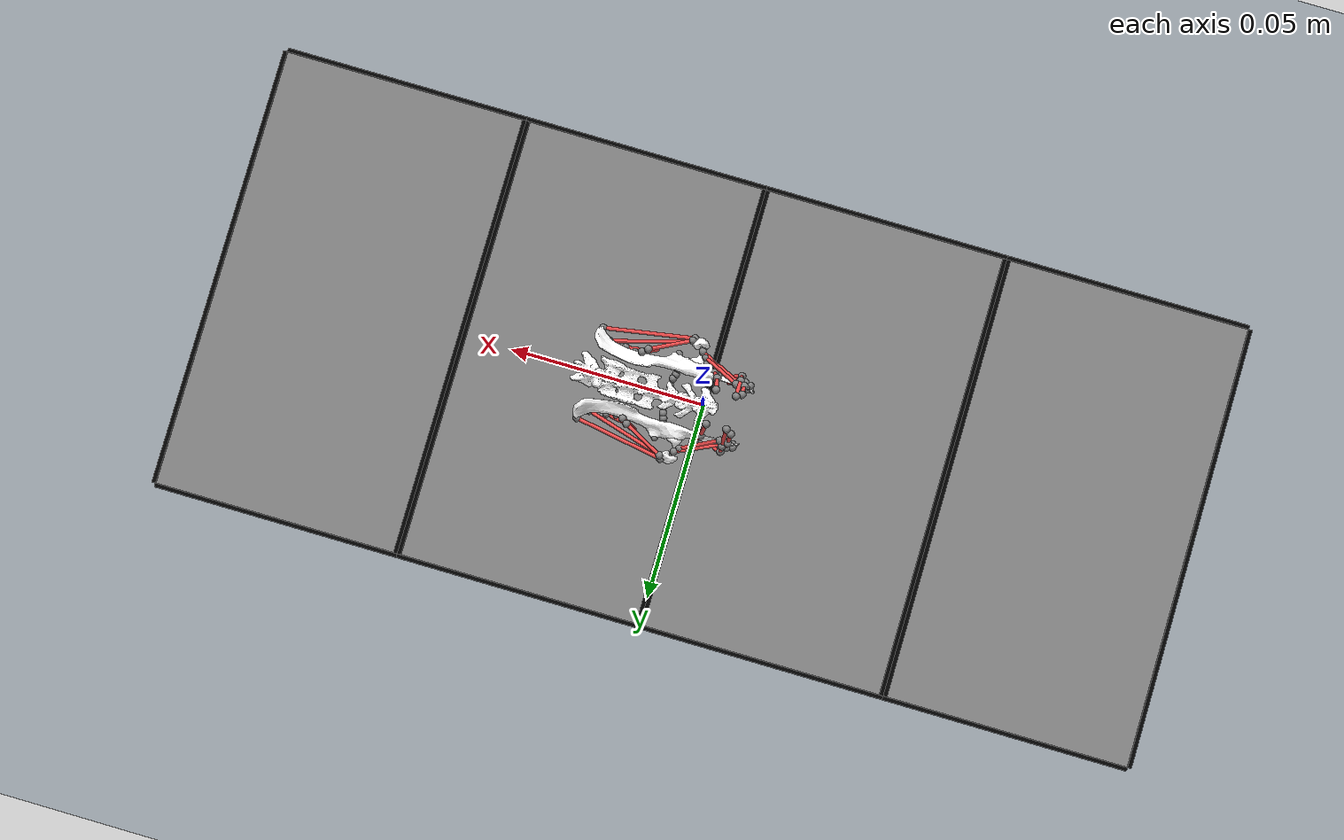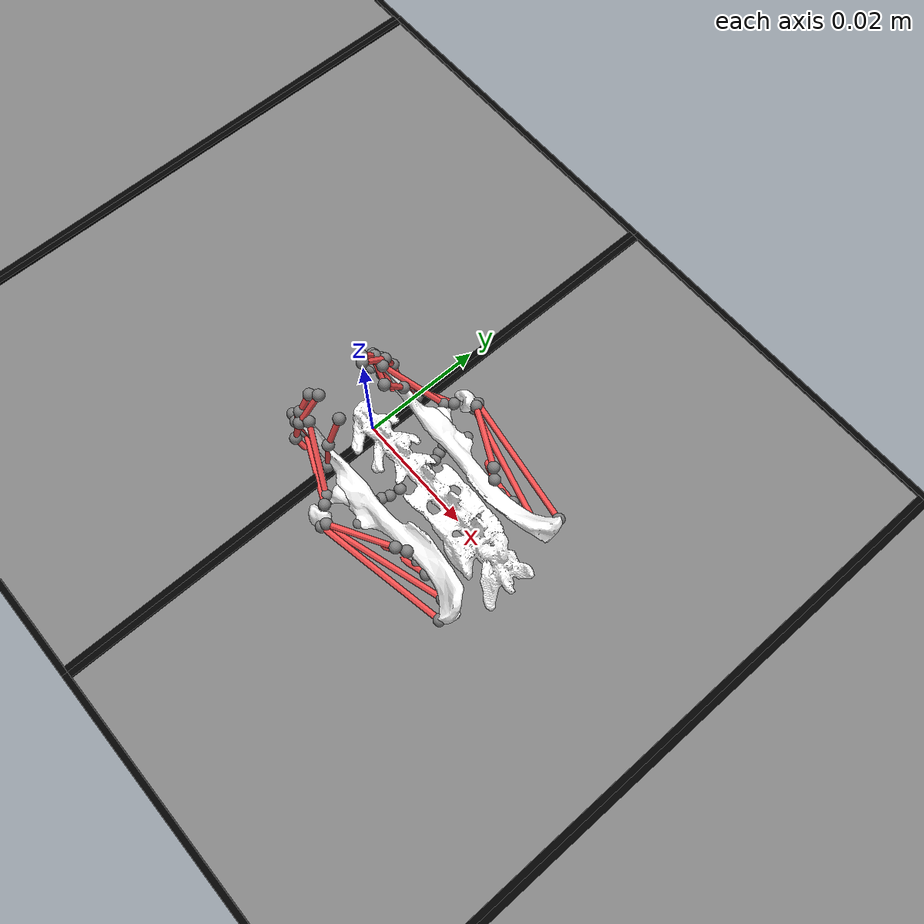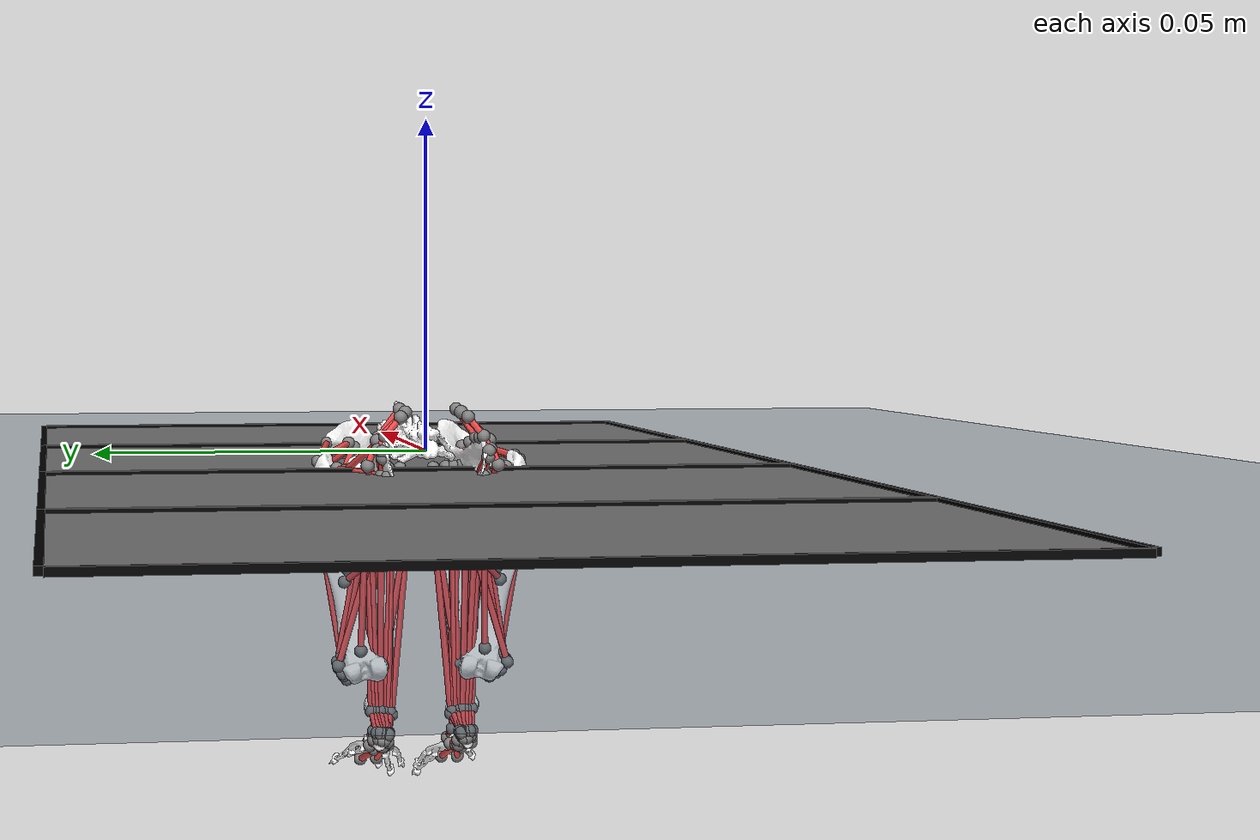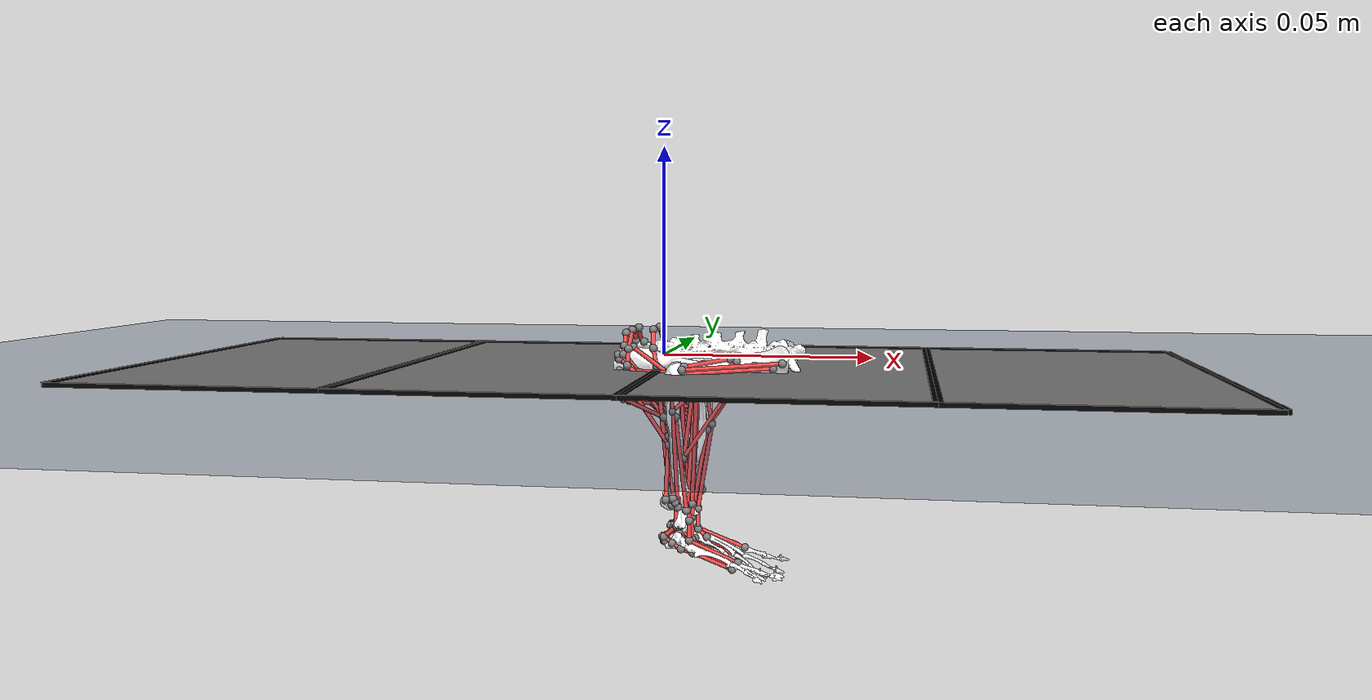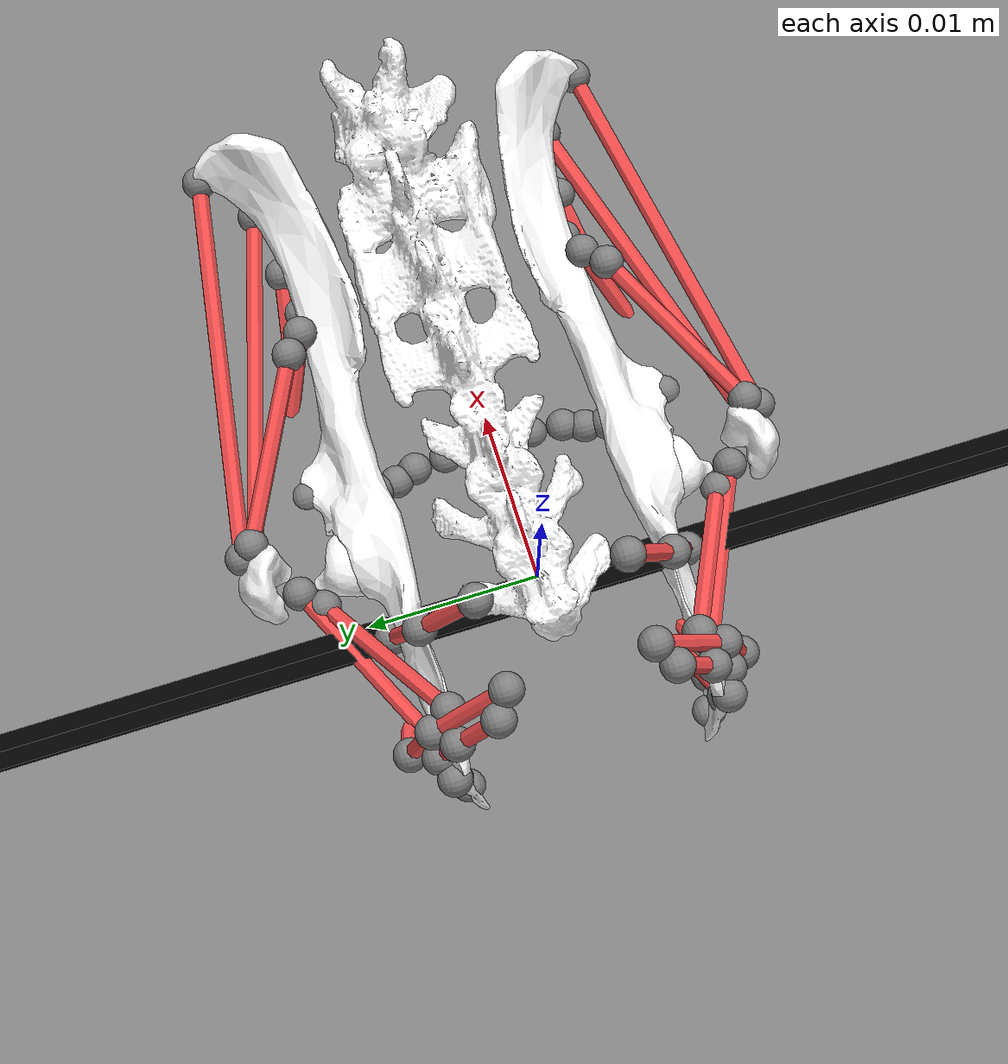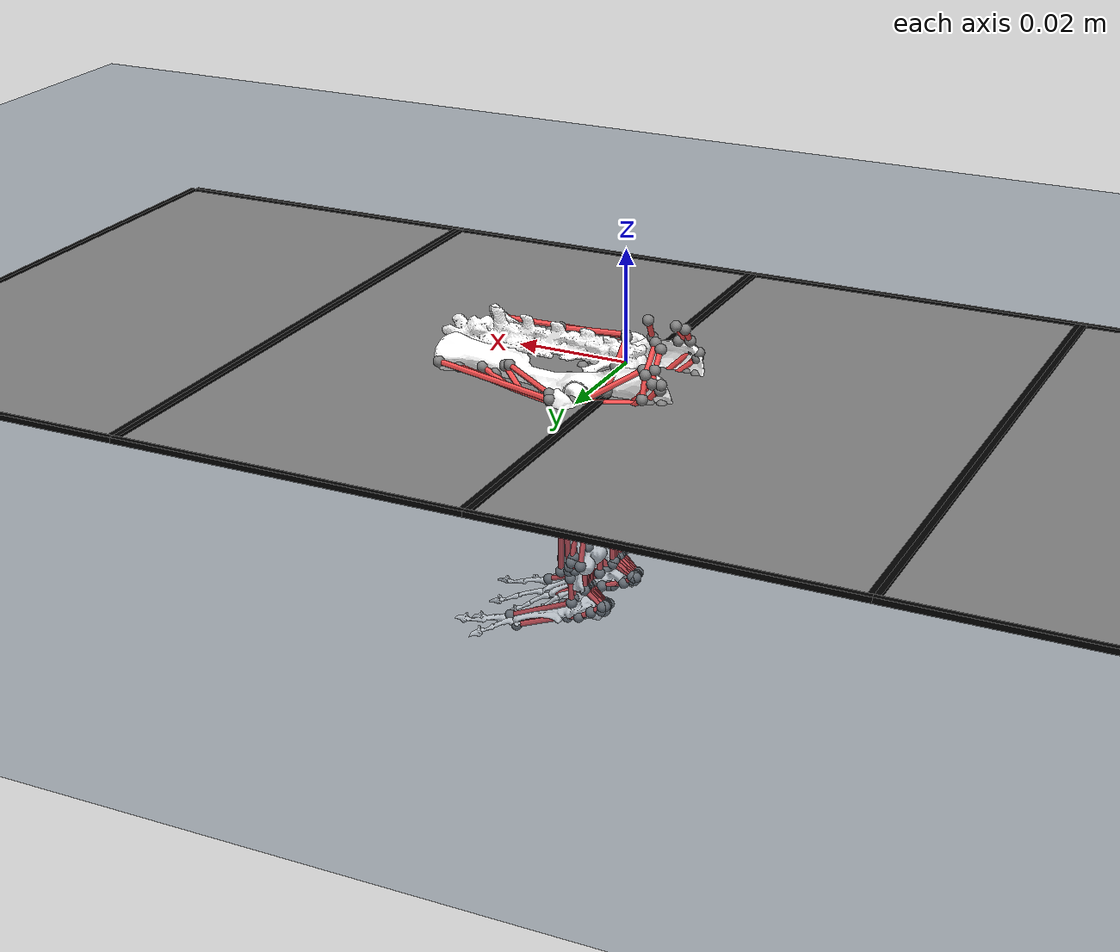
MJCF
<mujoco>
    <include file="converted/rat_hindlimb_bilateral_cvt2.xml"/>

    <visual>
        <headlight diffuse="0.6 0.6 0.6" ambient="0.3 0.3 0.3" specular="0 0 0"/>
        <rgba haze="0.15 0.25 0.35 1"/>
        <global azimuth="150" elevation="-20"/>
    </visual>

    <asset>
        <texture type="skybox" builtin="gradient" rgb1="0.3 0.5 0.7" rgb2="0 0 0" width="512" height="3072"/>
        <texture type="2d" name="groundplane" builtin="checker" mark="edge" rgb1="0.2 0.3 0.4" rgb2="0.1 0.2 0.3"
        markrgb="0.8 0.8 0.8" width="300" height="300"/>
        <material name="groundplane" texture="groundplane" texuniform="true" texrepeat="5 5" reflectance="0.2"/>
    </asset>
    <worldbody>
        <light pos="0 0 1.5" dir="0 0 -1" directional="false"/>
        <geom name="floor" size="0 0 .05" pos="0 0 -0.004" type="plane" material="groundplane"/>

        <!-- Force plates -->
        <body name="force_plate_1" pos="-0.09525 0.0 -0.003">
            <geom type="box" size="0.03175 5.71500015e-02 4.76837158e-09" rgba="0.5 0.5 0.5 1" contype="1"/>
            <!-- Borders for force_plate_1 -->
            <geom type="box" name="fp1_border_top"    pos="0 0.05765 0" size="0.03175 0.0005 0.0005" rgba="0 0 0 1"/>
            <geom type="box" name="fp1_border_bottom" pos="0 -0.05765 0" size="0.03175 0.0005 0.0005" rgba="0 0 0 1"/>
            <geom type="box" name="fp1_border_right"  pos="0.03225 0 0" size="0.0005 0.05715 0.0005" rgba="0 0 0 1"/>
            <geom type="box" name="fp1_border_left"   pos="-0.03225 0 0" size="0.0005 0.05715 0.0005" rgba="0 0 0 1"/>
        </body>
        <body name="force_plate_2" pos="-0.03175 0.0 -0.003">
            <geom type="box" size="0.03175 5.71500015e-02 4.76837158e-09" rgba="0.5 0.5 0.5 1" contype="1"/>
            <!-- Borders for force_plate_2 -->
            <geom type="box" name="fp2_border_top"    pos="0 0.05765 0" size="0.03175 0.0005 0.0005" rgba="0 0 0 1"/>
            <geom type="box" name="fp2_border_bottom" pos="0 -0.05765 0" size="0.03175 0.0005 0.0005" rgba="0 0 0 1"/>
            <geom type="box" name="fp2_border_right"  pos="0.03225 0 0" size="0.0005 0.05715 0.0005" rgba="0 0 0 1"/>
            <geom type="box" name="fp2_border_left"   pos="-0.03225 0 0" size="0.0005 0.05715 0.0005" rgba="0 0 0 1"/>
        </body>
        <body name="force_plate_3" pos="0.03175 0.0 -0.003">
            <geom type="box" size="0.03175 5.71500015e-02 4.76837158e-09" rgba="0.5 0.5 0.5 1" contype="1"/>
             <!-- Borders for force_plate_3 -->
            <geom type="box" name="fp3_border_top"    pos="0 0.05765 0" size="0.03175 0.0005 0.0005" rgba="0 0 0 1"/>
            <geom type="box" name="fp3_border_bottom" pos="0 -0.05765 0" size="0.03175 0.0005 0.0005" rgba="0 0 0 1"/>
            <geom type="box" name="fp3_border_right"  pos="0.03225 0 0" size="0.0005 0.05715 0.0005" rgba="0 0 0 1"/>
            <geom type="box" name="fp3_border_left"   pos="-0.03225 0 0" size="0.0005 0.05715 0.0005" rgba="0 0 0 1"/>
        </body>
        <body name="force_plate_4" pos="0.09525 0.0 -0.003">
            <geom type="box" size="0.03175 5.71500015e-02 4.76837158e-09" rgba="0.5 0.5 0.5 1" contype="1"/>
            <!-- Borders for force_plate_4 -->
            <geom type="box" name="fp4_border_top"    pos="0 0.05765 0" size="0.03175 0.0005 0.0005" rgba="0 0 0 1"/>
            <geom type="box" name="fp4_border_bottom" pos="0 -0.05765 0" size="0.03175 0.0005 0.0005" rgba="0 0 0 1"/>
            <geom type="box" name="fp4_border_right"  pos="0.03225 0 0" size="0.0005 0.05715 0.0005" rgba="0 0 0 1"/>
            <geom type="box" name="fp4_border_left"   pos="-0.03225 0 0" size="0.0005 0.05715 0.0005" rgba="0 0 0 1"/>
        </body>
    </worldbody>
</mujoco>

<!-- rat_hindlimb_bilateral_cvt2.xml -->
<mujoco model="template">
  <!-- This model has been converted from an OpenSim model. Model conversion by MyoConverter https://github.com/MyoHub/myoconverter. This model is licensed under Apache 2.0. -->
  <compiler angle="radian" autolimits="true"/>
  <size njmax="1000" nconmax="400" nkey="1" nuser_jnt="1"/>
  <visual>
    <scale framelength="0.5" framewidth="0.01"/>
  </visual>
  <statistic meansize="0.0392205" extent="2" center="0 0 0"/>
  <default class="main">
    <joint limited="true" armature="1e-05" damping="0.05"/>
    <site size="0.001 0.005 0.005"/>
    <tendon limited="false" width="0.0005" rgba="0.95 0.3 0.3 1"/>
    <default class="muscle">
      <general ctrllimited="true" ctrlrange="0 1" dyntype="muscle" gaintype="muscle" biastype="muscle" dynprm="0.01 0.04 0 0 0 0 0 0 0 0" gainprm="0.75 1.05 -1 200 0.5 1.6 1.5 1.3 1.2 0" biasprm="0.75 1.05 -1 200 0.5 1.6 1.5 1.3 1.2 0"/>
    </default>
    <default class="motor">
      <general gainprm="5 0 0 0 0 0 0 0 0 0"/>
    </default>
  </default>
  <asset>
    <mesh name="spine_geom_1_spine" file="Geometry/spine.stl"/>
    <mesh name="pelvis_r_geom_1_pelvis_r" file="Geometry/pelvis_r.stl"/>
    <mesh name="femur_r_geom_1_femur_r" file="Geometry/femur_r.stl"/>
    <mesh name="tibia_r_geom_1_tibia_r" file="Geometry/tibia_r.stl"/>
    <mesh name="foot_r_geom_1_foot_r" file="Geometry/foot_r.stl"/>
    <mesh name="pelvis_l_geom_1_pelvis_r" file="Geometry/pelvis_r.stl" scale="1 1 -1"/>
    <mesh name="femur_l_geom_1_femur_r" file="Geometry/femur_r.stl" scale="1 1 -1"/>
    <mesh name="tibia_l_geom_1_tibia_r" file="Geometry/tibia_r.stl" scale="1 1 -1"/>
    <mesh name="foot_l_geom_1_foot_r" file="Geometry/foot_r.stl" scale="1 1 -1"/>
  </asset>
  <worldbody>
    <body name="spine" quat="0.707035 0.707179 0 0">
      <inertial pos="0 0 0" mass="0.12" diaginertia="0.001 0.001 0.001"/>
      <joint name="sacrum_x" pos="0 0 0" axis="1 0 0" type="slide" range="-0.1 0.25" damping="0"/>
      <joint name="sacrum_y" pos="0 0 0" axis="0 1 0" type="slide" range="0 0.2" damping="0" user="0.05"/>
      <joint name="sacrum_z" pos="0 0 0" axis="0 0 1" type="slide" range="-0.1 0.1" damping="0"/>
      <joint name="sacrum_pitch" pos="0 0 0" axis="0 0 1" range="-1.571 1.571" damping="0" user="0.523599"/>
      <joint name="sacrum_roll" pos="0 0 0" axis="1 0 0" range="-1.571 1.571" damping="0"/>
      <joint name="sacrum_yaw" pos="0 0 0" axis="0 1 0" range="-1.571 1.571" damping="0"/>
      <geom name="spine_geom_1" type="mesh" rgba="1 1 1 1" mesh="spine_geom_1_spine"/>
      <site name="TAIL_marker" pos="-0.007971 0.007758 0" size="0.01" group="4" rgba="1 0.1 0.5 0.5"/>
      <site name="SPL6_marker" pos="0.03067 0.01512 0" size="0.01" group="4" rgba="1 0.1 0.5 0.5"/>
      <body name="pelvis_r" pos="0.005 -0.003 0.01">
        <inertial pos="0 0 0" mass="0.02" diaginertia="0.001 0.001 0.001"/>
        <joint name="sacroiliac_r_flx" pos="0 0 0" axis="0 0 1" range="-0.02301 0.1515" user="0.0645772"/>
        <geom name="pelvis_r_geom_1" type="mesh" rgba="1 1 1 1" mesh="pelvis_r_geom_1_pelvis_r"/>
        <site name="R_BFa_R_BFa_pelvis_r_origin_1" pos="-0.0121749 0.00924643 -0.00578144"/>
        <site name="R_BFa_R_BFa_pelvis_r_via_2" pos="-0.0122885 0.00508418 -0.00151152"/>
        <site name="R_BFa_R_BFa_pelvis_r_via_3" pos="-0.0123354 0.001285 -0.000120889"/>
        <site name="R_BFp_R_BFp_pelvis_r_origin_1" pos="-0.0148982 0.00358085 -0.00199087"/>
        <site name="R_CF_R_CF_pelvis_r_origin_1" pos="-0.00700731 0.00944849 -0.0056452"/>
        <site name="R_CF_R_CF_pelvis_r_via_2" pos="-0.00647922 0.00520385 -0.00255716"/>
        <site name="R_CF_R_CF_pelvis_r_via_3" pos="-0.00545092 0.00116543 -0.00108763"/>
        <site name="R_STp_R_STp_pelvis_r_origin_1" pos="-0.0146843 0.002602 -0.00208829"/>
        <site name="R_STa_R_STa_pelvis_r_origin_1" pos="-0.0135086 0.00858129 -0.00493706"/>
        <site name="R_STa_R_STa_pelvis_r_via_2" pos="-0.0134873 0.00569943 -0.00259459"/>
        <site name="R_STa_R_STa_pelvis_r_via_3" pos="-0.0134977 0.00375875 -0.00152466"/>
        <site name="R_SM_R_SM_pelvis_r_origin_1" pos="-0.0147235 -0.000233842 -0.00279779"/>
        <site name="R_QF_R_QF_pelvis_r_origin_1" pos="-0.0132552 -0.00240028 -0.0035466"/>
        <site name="R_TFL_R_TFL_pelvis_r_origin_1" pos="0.0154525 0.000729078 -0.00173771"/>
        <site name="R_GMa_R_GMa_pelvis_r_origin_1" pos="0.0135263 0.0025046 -0.00128258"/>
        <site name="R_GMe_R_GMe_pelvis_r_origin_1" pos="0.0245712 0.00252727 0.00178321"/>
        <site name="R_GMi_R_GMi_pelvis_r_origin_1" pos="0.0221635 0.00104939 -0.000834164"/>
        <site name="R_Pir_R_Pir_pelvis_r_origin_1" pos="0.0121189 0.00323606 -0.000256669"/>
        <site name="R_GP_R_GP_pelvis_r_origin_1" pos="-0.0139682 -0.00441352 -0.00523475"/>
        <site name="R_GA_R_GA_pelvis_r_origin_1" pos="-0.0134444 -0.00825039 -0.00858154"/>
        <site name="R_AL_R_AL_pelvis_r_origin_1" pos="-0.00459175 -0.00542911 -0.00584408"/>
        <site name="R_AM_R_AM_pelvis_r_origin_1" pos="-0.0121854 -0.00829689 -0.00859813"/>
        <site name="R_AB_R_AB_pelvis_r_origin_1" pos="-0.0116082 -0.00729487 -0.00792992"/>
        <site name="R_Pec_R_Pec_pelvis_r_origin_1" pos="-0.0148211 -0.00771845 -0.00768263"/>
        <site name="R_IP_R_IP_pelvis_r_origin_1" pos="0.020316 -0.00119061 -0.00242288"/>
        <site name="R_OE_R_OE_pelvis_r_origin_1" pos="-0.00902669 -0.00153646 -0.00325204"/>
        <site name="R_OI_R_OI_pelvis_r_origin_1" pos="-0.0127147 -0.000119353 -0.00218658"/>
        <site name="R_GS_R_GS_pelvis_r_origin_1" pos="0.0178456 0.00154777 -0.00135023"/>
        <site name="R_GI_R_GI_pelvis_r_origin_1" pos="-0.0114102 0.00542928 -0.00270696"/>
        <site name="R_RF_R_RF_pelvis_r_origin_1" pos="0.00459962 -0.000458644 0.0010492"/>
        <site name="RASI_marker" pos="0.028 0.004 0.003" size="0.01" group="4" rgba="1 0.1 0.5 0.5"/>
        <site name="RHIP_marker" pos="-0.001 0.001 0.01" size="0.01" group="4" rgba="1 0.1 0.5 0.5"/>
        <body name="femur_r">
          <inertial pos="0 -0.015 0" quat="0.707107 0.707107 0 0" mass="0.02" diaginertia="0.001 0.001 0.001"/>
          <joint name="hip_r_flx" pos="0 0 0" axis="0 0 1" range="-0.8727 1.222" user="0.698132"/>
          <joint name="hip_r_add" pos="0 0 0" axis="1 0 0" range="-0.8727 0.3491" user="-0.174533"/>
          <joint name="hip_r_int" pos="0 0 0" axis="0 1 0" range="-0.8727 0.6981"/>
          <geom name="femur_r_geom_1" type="mesh" rgba="1 1 1 1" mesh="femur_r_geom_1_femur_r"/>
          <site name="R_CF_R_CF_femur_r_insertion_4" pos="-0.00233532 -0.0278301 -0.00033572"/>
          <site name="R_QF_R_QF_femur_r_insertion_2" pos="-0.00285983 -0.00124395 0.00518669"/>
          <site name="R_TFL_R_TFL_femur_r_insertion_2" pos="0.0013429 -0.0203484 0.00167228"/>
          <site name="R_GMa_R_GMa_femur_r_insertion_2" pos="-0.000663997 -0.00857737 0.00575644"/>
          <site name="R_GMe_R_GMe_femur_r_insertion_2" pos="0.00169107 0.00107141 0.0057686"/>
          <site name="R_GMi_R_GMi_femur_r_insertion_2" pos="0.00169813 4.48958e-05 0.00506843"/>
          <site name="R_Pir_R_Pir_femur_r_insertion_2" pos="0.00207348 0.0017137 0.00504137"/>
          <site name="R_AL_R_AL_femur_r_insertion_2" pos="-0.00200273 -0.0151796 0.00166969"/>
          <site name="R_AB_R_AB_femur_r_insertion_2" pos="-0.00192481 -0.0171927 0.0021014"/>
          <site name="R_Pec_R_Pec_femur_r_insertion_2" pos="-0.00287201 -0.0103114 0.00381355"/>
          <site name="R_IP_R_IP_femur_r_insertion_2" pos="-0.000597475 -0.00409587 0.00135809"/>
          <site name="R_OE_R_OE_femur_r_insertion_2" pos="-0.00233645 -0.00121543 0.00175677"/>
          <site name="R_OI_R_OI_femur_r_via_2" pos="-0.00107151 0.000172028 0.0031543"/>
          <site name="R_GS_R_GS_femur_r_insertion_2" pos="-0.000167442 -0.00603465 0.0020778"/>
          <site name="R_GI_R_GI_femur_r_insertion_2" pos="-0.00216784 -9.46528e-05 0.00200781"/>
          <site name="R_RF_R_RF_femur_r_via_2" pos="0.00303536 -0.0317148 -0.00146523"/>
          <site name="R_VL_R_VL_femur_r_origin_1" pos="-0.000569833 -0.00364222 0.00667474"/>
          <site name="R_VL_R_VL_femur_r_via_2" pos="0.000128525 -0.0319382 0.00197687"/>
          <site name="R_VI_R_VI_femur_r_origin_1" pos="7.12541e-05 -0.0100785 0.00480287"/>
          <site name="R_VI_R_VI_femur_r_via_2" pos="0.00209779 -0.0328457 0.00121274"/>
          <site name="R_VM_R_VM_femur_r_origin_1" pos="-0.000544653 -0.00501067 0.00147071"/>
          <site name="R_VM_R_VM_femur_r_via_2" pos="0.00186154 -0.0317413 -0.00348656"/>
          <site name="R_MG_R_MG_femur_r_origin_1" pos="-0.000356504 -0.0302327 -0.00437238"/>
          <site name="R_LG_R_LG_femur_r_origin_1" pos="-0.000830728 -0.0296591 0.0030687"/>
          <site name="R_Pla_R_Pla_femur_r_origin_1" pos="-0.000947694 -0.028816 0.0024527"/>
          <site name="R_EDL_R_EDL_femur_r_origin_1" pos="-0.00115765 -0.0313677 0.00233691"/>
          <site name="R_Pop_R_Pop_femur_r_origin_1" pos="-0.000334756 -0.030686 0.00277048"/>
          <site name="R_Pop_R_Pop_femur_r_via_2" pos="-0.0025438 -0.030008 0.00314105"/>
          <site name="RKNE_marker" pos="0 -0.035 0.003" size="0.01" group="4" rgba="1 0.1 0.5 0.5"/>
          <body name="tibia_r" pos="0.00057 -0.03996 -0.003816">
            <inertial pos="0 0.015 0" quat="0.707107 0.707107 0 0" mass="0.02" diaginertia="0.001 0.001 0.001"/>
            <joint name="knee_r_translation1" pos="0 0 0" axis="1 0 0" type="slide" range="-0.005239 -0.001413" user="-0.00347295"/>
            <joint name="knee_r_translation2" pos="0 0 0" axis="0 1 0" type="slide" range="-0.03425 -0.03206" user="-0.0339632"/>
            <joint name="knee_r_translation3" pos="0 0 0" axis="0 0 1" type="slide" range="0.002381 0.002904" user="0.00290105"/>
            <joint name="knee_r_flx" pos="0 0 0" axis="0 0 1" range="-2.618 -0.3491" user="-2.0944"/>
            <joint name="knee_r_rotation2" pos="0 0 0" axis="1 0 0" range="-0.08727 0.06458" user="-0.0523844"/>
            <joint name="knee_r_rotation3" pos="0 0 0" axis="0 1 0" limited="false" range="-2.618 -0.3491" user="-2.0944"/>
            <geom name="tibia_r_geom_1" type="mesh" rgba="1 1 1 1" mesh="tibia_r_geom_1_tibia_r"/>
            <site name="R_BFa_R_BFa_tibia_r_insertion_4" pos="-0.00297205 0.0325031 0.00135646"/>
            <site name="R_BFp_R_BFp_tibia_r_via_2" pos="-0.00334773 0.027051 0.000585165"/>
            <site name="R_BFp_R_BFp_tibia_r_insertion_3" pos="0.00207783 0.0274099 0.000130431"/>
            <site name="R_STp_R_STp_tibia_r_insertion_2" pos="0.00200828 0.0276058 -0.00209032"/>
            <site name="R_STa_R_STa_tibia_r_insertion_4" pos="0.00200828 0.0276058 -0.00209032"/>
            <site name="R_SM_R_SM_tibia_r_insertion_2" pos="0.00053037 0.0342271 -0.00269725"/>
            <site name="R_GP_R_GP_tibia_r_insertion_2" pos="0.00199824 0.0284325 -0.00281468"/>
            <site name="R_GA_R_GA_tibia_r_insertion_2" pos="0.00155229 0.0308279 -0.0028166"/>
            <site name="R_AM_R_AM_tibia_r_insertion_2" pos="0.000903098 0.0324771 -0.00273851"/>
            <site name="R_RF_R_RF_tibia_r_via_3" pos="0.00370614 0.0398571 -0.00161563"/>
            <site name="R_VL_R_VL_tibia_r_via_3" pos="0.00299627 0.0402266 0.000888015"/>
            <site name="R_VL_R_VL_tibia_r_insertion_4" pos="0.00495263 0.0355954 -0.000407924"/>
            <site name="R_VI_R_VI_tibia_r_via_3" pos="0.00325472 0.0399158 -0.000376213"/>
            <site name="R_VI_R_VI_tibia_r_insertion_4" pos="0.00495263 0.0355954 -0.000407924"/>
            <site name="R_VM_R_VM_tibia_r_via_3" pos="0.00386909 0.0397091 -0.00355365"/>
            <site name="R_VM_R_VM_tibia_r_insertion_4" pos="0.00495263 0.0355954 -0.000407924"/>
            <site name="R_MG_R_MG_tibia_r_via_2" pos="-0.000610285 0.0344712 -0.00453793"/>
            <site name="R_MG_R_MG_tibia_r_via_3" pos="-0.00101296 0.00180707 -0.00152389"/>
            <site name="R_LG_R_LG_tibia_r_via_2" pos="-0.00341142 0.0351877 0.00275941"/>
            <site name="R_LG_R_LG_tibia_r_via_3" pos="-0.00133264 0.00254948 0.00129734"/>
            <site name="R_Pla_R_Pla_tibia_r_via_2" pos="-0.00359399 0.0343827 0.00205396"/>
            <site name="R_Pla_R_Pla_tibia_r_via_3" pos="-0.00131222 0.00254091 0.000895373"/>
            <site name="R_Sol_R_Sol_tibia_r_origin_1" pos="-0.0037947 0.0344272 0.00036984"/>
            <site name="R_Sol_R_Sol_tibia_r_via_2" pos="-0.00128157 0.00252805 0.000291988"/>
            <site name="R_TA_R_TA_tibia_r_origin_1" pos="0.00381534 0.0350399 -0.00203202"/>
            <site name="R_TA_R_TA_tibia_r_via_2" pos="0.00544197 0.0254747 -0.00157899"/>
            <site name="R_TA_R_TA_tibia_r_via_3" pos="0.00186501 0.00401084 -0.000692755"/>
            <site name="R_EDL_R_EDL_tibia_r_via_2" pos="-0.000333626 0.0375621 0.00269411"/>
            <site name="R_EDL_R_EDL_tibia_r_via_3" pos="0.00163586 0.00386315 0.00111794"/>
            <site name="R_TP_R_TP_tibia_r_origin_1" pos="-0.00187978 0.0326057 -0.00148873"/>
            <site name="R_TP_R_TP_tibia_r_via_2" pos="-0.0011105 0.00195986 -0.000909166"/>
            <site name="R_FDL_R_FDL_tibia_r_origin_1" pos="-0.00214173 0.0344002 -0.000896069"/>
            <site name="R_FDL_R_FDL_tibia_r_via_2" pos="-0.000986225 0.00241095 -0.000541185"/>
            <site name="R_FHL_R_FHL_tibia_r_origin_1" pos="-0.000684791 0.0323426 -0.00142243"/>
            <site name="R_FHL_R_FHL_tibia_r_via_2" pos="-0.00108991 0.00225163 -0.00126701"/>
            <site name="R_Per_R_Per_tibia_r_origin_1" pos="-0.00224094 0.0356028 0.00278697"/>
            <site name="R_Per_R_Per_tibia_r_via_2" pos="-0.00135112 0.00255723 0.00166131"/>
            <site name="R_Pop_R_Pop_tibia_r_via_3" pos="-0.00324222 0.0349346 -0.000476873"/>
            <site name="R_Pop_R_Pop_tibia_r_insertion_4" pos="0.0018743 0.0256924 -0.00219991"/>
            <site name="RANK_marker" pos="0 0 0.004" size="0.01" group="4" rgba="1 0.1 0.5 0.5"/>
            <body name="foot_r">
              <inertial pos="0.007 -0.005 0" quat="0.5 0.5 0.5 0.5" mass="0.02" diaginertia="0.001 0.001 0.001"/>
              <joint name="ankle_r_translation1" pos="0 0 0" axis="1 0 0" type="slide" range="-1e-06 0"/>
              <joint name="ankle_r_translation2" pos="0 0 0" axis="0 1 0" type="slide" range="-1e-06 0"/>
              <joint name="ankle_r_translation3" pos="0 0 0" axis="0 0 1" type="slide" range="-1e-06 0"/>
              <joint name="ankle_r_flx" pos="0 0 0" axis="0 0 1" range="-0.5236 1.047" user="0.872665"/>
              <joint name="ankle_r_add" pos="0 0 0" axis="1 0 0" range="-0.08727 0.6109" user="-0.0872665"/>
              <joint name="ankle_r_int" pos="0 0 0" axis="0 1 0" range="-0.8727 0.2618"/>
              <geom name="foot_r_geom_1" type="mesh" rgba="1 1 1 1" mesh="foot_r_geom_1_foot_r"/>
              <site name="R_MG_R_MG_foot_r_via_4" pos="-0.00436449 -0.000415019 -0.000610899"/>
              <site name="R_MG_R_MG_foot_r_insertion_5" pos="-0.0042571 -0.0014281 -8.03269e-05"/>
              <site name="R_LG_R_LG_foot_r_via_4" pos="-0.00489425 -0.000289436 0.000786158"/>
              <site name="R_LG_R_LG_foot_r_insertion_5" pos="-0.00423576 -0.00127028 0.000886939"/>
              <site name="R_Pla_R_Pla_foot_r_via_4" pos="-0.00488749 -0.000344109 0.000389473"/>
              <site name="R_Pla_R_Pla_foot_r_insertion_5" pos="-0.00460193 -0.00146048 0.000370143"/>
              <site name="R_Sol_R_Sol_foot_r_via_3" pos="-0.00485512 -0.00039237 7.70798e-05"/>
              <site name="R_Sol_R_Sol_foot_r_insertion_4" pos="-0.00458519 -0.00147388 4.84638e-05"/>
              <site name="R_TA_R_TA_foot_r_via_4" pos="0.0019962 -0.00113777 -0.000811539"/>
              <site name="R_TA_R_TA_foot_r_insertion_5" pos="0.00420238 -0.00291829 -0.00125573"/>
              <site name="R_EDL_R_EDL_foot_r_via_4" pos="0.00157412 -0.00108978 0.000869418"/>
              <site name="R_EDL_R_EDL_foot_r_insertion_5" pos="0.0133904 -0.00585533 0.00150717"/>
              <site name="R_TP_R_TP_foot_r_via_3" pos="-0.00501409 -0.000484128 -0.000497051"/>
              <site name="R_TP_R_TP_foot_r_via_4" pos="-0.00280089 -0.00209869 -0.000250524"/>
              <site name="R_TP_R_TP_foot_r_insertion_5" pos="0.00130182 -0.00332176 -0.00125588"/>
              <site name="R_FDL_R_FDL_foot_r_via_3" pos="-0.00490061 -0.00042816 -0.000278346"/>
              <site name="R_FDL_R_FDL_foot_r_via_4" pos="-0.00301935 -0.00181179 -4.9272e-05"/>
              <site name="R_FDL_R_FDL_foot_r_via_5" pos="-0.000466477 -0.00324499 -0.000275292"/>
              <site name="R_FDL_R_FDL_foot_r_insertion_6" pos="0.0120885 -0.00745259 0.00167985"/>
              <site name="R_FHL_R_FHL_foot_r_via_3" pos="-0.00465502 -0.000589998 -0.00060064"/>
              <site name="R_FHL_R_FHL_foot_r_via_4" pos="-0.00276688 -0.00206989 -0.00067195"/>
              <site name="R_FHL_R_FHL_foot_r_via_5" pos="0.00020941 -0.00338633 -0.00047099"/>
              <site name="R_FHL_R_FHL_foot_r_insertion_6" pos="0.0121609 -0.00740549 -0.000922227"/>
              <site name="R_Per_R_Per_foot_r_via_3" pos="-0.00452309 -0.000315681 0.00115711"/>
              <site name="R_Per_R_Per_foot_r_via_4" pos="-0.00247989 -0.0017431 0.00143398"/>
              <site name="R_Per_R_Per_foot_r_via_5" pos="-0.000270516 -0.00299293 0.00176084"/>
              <site name="R_Per_R_Per_foot_r_insertion_6" pos="0.00242893 -0.00409792 0.000727718"/>
              <site name="RTOE_marker" pos="0.015 -0.005 0.005" size="0.01" group="4" rgba="1 0.1 0.5 0.5"/>
            </body>
          </body>
        </body>
      </body>
      <body name="pelvis_l" pos="0.005 -0.003 -0.01">
        <inertial pos="0 0 0" mass="0.02" diaginertia="0.001 0.001 0.001"/>
        <joint name="sacroiliac_l_flx" pos="0 0 0" axis="0 0 1" range="-0.02301 0.1515" user="0.0645772"/>
        <geom name="pelvis_l_geom_1" type="mesh" rgba="1 1 1 1" mesh="pelvis_l_geom_1_pelvis_r"/>
        <site name="L_BFa_L_BFa_pelvis_l_origin_1" pos="-0.0121749 0.00924643 0.00578144"/>
        <site name="L_BFa_L_BFa_pelvis_l_via_2" pos="-0.0122885 0.00508418 0.00151152"/>
        <site name="L_BFa_L_BFa_pelvis_l_via_3" pos="-0.0123354 0.001285 0.000120889"/>
        <site name="L_BFp_L_BFp_pelvis_l_origin_1" pos="-0.0148982 0.00358085 0.00199087"/>
        <site name="L_CF_L_CF_pelvis_l_origin_1" pos="-0.00700731 0.00944849 0.0056452"/>
        <site name="L_CF_L_CF_pelvis_l_via_2" pos="-0.00647922 0.00520385 0.00255716"/>
        <site name="L_CF_L_CF_pelvis_l_via_3" pos="-0.00545092 0.00116543 0.00108763"/>
        <site name="L_STp_L_STp_pelvis_l_origin_1" pos="-0.0146843 0.002602 0.00208829"/>
        <site name="L_STa_L_STa_pelvis_l_origin_1" pos="-0.0135086 0.00858129 0.00493706"/>
        <site name="L_STa_L_STa_pelvis_l_via_2" pos="-0.0134873 0.00569943 0.00259459"/>
        <site name="L_STa_L_STa_pelvis_l_via_3" pos="-0.0134977 0.00375875 0.00152466"/>
        <site name="L_SM_L_SM_pelvis_l_origin_1" pos="-0.0147235 -0.000233842 0.00279779"/>
        <site name="L_QF_L_QF_pelvis_l_origin_1" pos="-0.0132552 -0.00240028 0.0035466"/>
        <site name="L_TFL_L_TFL_pelvis_l_origin_1" pos="0.0154525 0.000729078 0.00173771"/>
        <site name="L_GMa_L_GMa_pelvis_l_origin_1" pos="0.0135263 0.0025046 0.00128258"/>
        <site name="L_GMe_L_GMe_pelvis_l_origin_1" pos="0.0245712 0.00252727 -0.00178321"/>
        <site name="L_GMi_L_GMi_pelvis_l_origin_1" pos="0.0221635 0.00104939 0.000834164"/>
        <site name="L_Pir_L_Pir_pelvis_l_origin_1" pos="0.0121189 0.00323606 0.000256669"/>
        <site name="L_GP_L_GP_pelvis_l_origin_1" pos="-0.0139682 -0.00441352 0.00523475"/>
        <site name="L_GA_L_GA_pelvis_l_origin_1" pos="-0.0134444 -0.00825039 0.00858154"/>
        <site name="L_AL_L_AL_pelvis_l_origin_1" pos="-0.00459175 -0.00542911 0.00584408"/>
        <site name="L_AM_L_AM_pelvis_l_origin_1" pos="-0.0121854 -0.00829689 0.00859813"/>
        <site name="L_AB_L_AB_pelvis_l_origin_1" pos="-0.0116082 -0.00729487 0.00792992"/>
        <site name="L_Pec_L_Pec_pelvis_l_origin_1" pos="-0.0148211 -0.00771845 0.00768263"/>
        <site name="L_IP_L_IP_pelvis_l_origin_1" pos="0.020316 -0.00119061 0.00242288"/>
        <site name="L_OE_L_OE_pelvis_l_origin_1" pos="-0.00902669 -0.00153646 0.00325204"/>
        <site name="L_OI_L_OI_pelvis_l_origin_1" pos="-0.0127147 -0.000119353 0.00218658"/>
        <site name="L_GS_L_GS_pelvis_l_origin_1" pos="0.0178456 0.00154777 0.00135023"/>
        <site name="L_GI_L_GI_pelvis_l_origin_1" pos="-0.0114102 0.00542928 0.00270696"/>
        <site name="L_RF_L_RF_pelvis_l_origin_1" pos="0.00459962 -0.000458644 -0.0010492"/>
        <site name="LASI_marker" pos="0.028 0.004 -0.003" size="0.01" group="4" rgba="1 0.1 0.5 0.5"/>
        <site name="LHIP_marker" pos="-0.001 0.001 -0.01" size="0.01" group="4" rgba="1 0.1 0.5 0.5"/>
        <body name="femur_l">
          <inertial pos="0 -0.015 0" quat="0.707107 0.707107 0 0" mass="0.02" diaginertia="0.001 0.001 0.001"/>
          <joint name="hip_l_flx" pos="0 0 0" axis="0 0 1" range="-0.8727 1.222" user="0.698132"/>
          <joint name="hip_l_add" pos="0 0 0" axis="-1 0 0" range="-0.8727 0.3491" user="0.174533"/>
          <joint name="hip_l_int" pos="0 0 0" axis="0 -1 0" range="-0.8727 0.6981"/>
          <geom name="femur_l_geom_1" type="mesh" rgba="1 1 1 1" mesh="femur_l_geom_1_femur_r"/>
          <site name="L_CF_L_CF_femur_l_insertion_4" pos="-0.00233532 -0.0278301 0.00033572"/>
          <site name="L_QF_L_QF_femur_l_insertion_2" pos="-0.00285983 -0.00124395 -0.00518669"/>
          <site name="L_TFL_L_TFL_femur_l_insertion_2" pos="0.0013429 -0.0203484 -0.00167228"/>
          <site name="L_GMa_L_GMa_femur_l_insertion_2" pos="-0.000663997 -0.00857737 -0.00575644"/>
          <site name="L_GMe_L_GMe_femur_l_insertion_2" pos="0.00169107 0.00107141 -0.0057686"/>
          <site name="L_GMi_L_GMi_femur_l_insertion_2" pos="0.00169813 4.48958e-05 -0.00506843"/>
          <site name="L_Pir_L_Pir_femur_l_insertion_2" pos="0.00207348 0.0017137 -0.00504137"/>
          <site name="L_AL_L_AL_femur_l_insertion_2" pos="-0.00200273 -0.0151796 -0.00166969"/>
          <site name="L_AB_L_AB_femur_l_insertion_2" pos="-0.00192481 -0.0171927 -0.0021014"/>
          <site name="L_Pec_L_Pec_femur_l_insertion_2" pos="-0.00287201 -0.0103114 -0.00381355"/>
          <site name="L_IP_L_IP_femur_l_insertion_2" pos="-0.000597475 -0.00409587 -0.00135809"/>
          <site name="L_OE_L_OE_femur_l_insertion_2" pos="-0.00233645 -0.00121543 -0.00175677"/>
          <site name="L_OI_L_OI_femur_l_via_2" pos="-0.00107151 0.000172028 -0.0031543"/>
          <site name="L_GS_L_GS_femur_l_insertion_2" pos="-0.000167442 -0.00603465 -0.0020778"/>
          <site name="L_GI_L_GI_femur_l_insertion_2" pos="-0.00216784 -9.46528e-05 -0.00200781"/>
          <site name="L_RF_L_RF_femur_l_via_2" pos="0.00303536 -0.0317148 0.00146523"/>
          <site name="L_VL_L_VL_femur_l_origin_1" pos="-0.000569833 -0.00364222 -0.00667474"/>
          <site name="L_VL_L_VL_femur_l_via_2" pos="0.000128525 -0.0319382 -0.00197687"/>
          <site name="L_VI_L_VI_femur_l_origin_1" pos="7.12541e-05 -0.0100785 -0.00480287"/>
          <site name="L_VI_L_VI_femur_l_via_2" pos="0.00209779 -0.0328457 -0.00121274"/>
          <site name="L_VM_L_VM_femur_l_origin_1" pos="-0.000544653 -0.00501067 -0.00147071"/>
          <site name="L_VM_L_VM_femur_l_via_2" pos="0.00186154 -0.0317413 0.00348656"/>
          <site name="L_MG_L_MG_femur_l_origin_1" pos="-0.000356504 -0.0302327 0.00437238"/>
          <site name="L_LG_L_LG_femur_l_origin_1" pos="-0.000830728 -0.0296591 -0.0030687"/>
          <site name="L_Pla_L_Pla_femur_l_origin_1" pos="-0.000947694 -0.028816 -0.0024527"/>
          <site name="L_EDL_L_EDL_femur_l_origin_1" pos="-0.00115765 -0.0313677 -0.00233691"/>
          <site name="L_Pop_L_Pop_femur_l_origin_1" pos="-0.000334756 -0.030686 -0.00277048"/>
          <site name="L_Pop_L_Pop_femur_l_via_2" pos="-0.0025438 -0.030008 -0.00314105"/>
          <site name="LKNE_marker" pos="0 -0.035 -0.003" size="0.01" group="4" rgba="1 0.1 0.5 0.5"/>
          <body name="tibia_l" pos="0.00057 -0.03996 0.003816">
            <inertial pos="0 0.015 0" quat="0.707107 0.707107 0 0" mass="0.02" diaginertia="0.001 0.001 0.001"/>
            <joint name="knee_l_translation1" pos="0 0 0" axis="1 0 0" type="slide" range="-0.005239 -0.001413" user="-0.00347295"/>
            <joint name="knee_l_translation2" pos="0 0 0" axis="0 1 0" type="slide" range="-0.03425 -0.03206" user="-0.0339632"/>
            <joint name="knee_l_translation3" pos="0 0 0" axis="0 0 1" type="slide" range="-0.002904 -0.002381" user="-0.00290105"/>
            <joint name="knee_l_flx" pos="0 0 0" axis="0 0 1" range="-2.618 -0.3491" user="-2.0944"/>
            <joint name="knee_l_rotation2" pos="0 0 0" axis="1 0 0" range="-0.06458 0.08727" user="0.0523844"/>
            <joint name="knee_l_rotation3" pos="0 0 0" axis="0 1 0" limited="false" range="-2.618 -0.3491" user="-2.0944"/>
            <geom name="tibia_l_geom_1" type="mesh" rgba="1 1 1 1" mesh="tibia_l_geom_1_tibia_r"/>
            <site name="L_BFa_L_BFa_tibia_l_insertion_4" pos="-0.00297205 0.0325031 -0.00135646"/>
            <site name="L_BFp_L_BFp_tibia_l_via_2" pos="-0.00334773 0.027051 -0.000585165"/>
            <site name="L_BFp_L_BFp_tibia_l_insertion_3" pos="0.00207783 0.0274099 -0.000130431"/>
            <site name="L_STp_L_STp_tibia_l_insertion_2" pos="0.00200828 0.0276058 0.00209032"/>
            <site name="L_STa_L_STa_tibia_l_insertion_4" pos="0.00200828 0.0276058 0.00209032"/>
            <site name="L_SM_L_SM_tibia_l_insertion_2" pos="0.00053037 0.0342271 0.00269725"/>
            <site name="L_GP_L_GP_tibia_l_insertion_2" pos="0.00199824 0.0284325 0.00281468"/>
            <site name="L_GA_L_GA_tibia_l_insertion_2" pos="0.00155229 0.0308279 0.0028166"/>
            <site name="L_AM_L_AM_tibia_l_insertion_2" pos="0.000903098 0.0324771 0.00273851"/>
            <site name="L_RF_L_RF_tibia_l_via_3" pos="0.00370614 0.0398571 0.00161563"/>
            <site name="L_VL_L_VL_tibia_l_via_3" pos="0.00299627 0.0402266 -0.000888015"/>
            <site name="L_VL_L_VL_tibia_l_insertion_4" pos="0.00495263 0.0355954 0.000407924"/>
            <site name="L_VI_L_VI_tibia_l_via_3" pos="0.00325472 0.0399158 0.000376213"/>
            <site name="L_VI_L_VI_tibia_l_insertion_4" pos="0.00495263 0.0355954 0.000407924"/>
            <site name="L_VM_L_VM_tibia_l_via_3" pos="0.00386909 0.0397091 0.00355365"/>
            <site name="L_VM_L_VM_tibia_l_insertion_4" pos="0.00495263 0.0355954 0.000407924"/>
            <site name="L_MG_L_MG_tibia_l_via_2" pos="-0.000610285 0.0344712 0.00453793"/>
            <site name="L_MG_L_MG_tibia_l_via_3" pos="-0.00101296 0.00180707 0.00152389"/>
            <site name="L_LG_L_LG_tibia_l_via_2" pos="-0.00341142 0.0351877 -0.00275941"/>
            <site name="L_LG_L_LG_tibia_l_via_3" pos="-0.00133264 0.00254948 -0.00129734"/>
            <site name="L_Pla_L_Pla_tibia_l_via_2" pos="-0.00359399 0.0343827 -0.00205396"/>
            <site name="L_Pla_L_Pla_tibia_l_via_3" pos="-0.00131222 0.00254091 -0.000895373"/>
            <site name="L_Sol_L_Sol_tibia_l_origin_1" pos="-0.0037947 0.0344272 -0.00036984"/>
            <site name="L_Sol_L_Sol_tibia_l_via_2" pos="-0.00128157 0.00252805 -0.000291988"/>
            <site name="L_TA_L_TA_tibia_l_origin_1" pos="0.00381534 0.0350399 0.00203202"/>
            <site name="L_TA_L_TA_tibia_l_via_2" pos="0.00544197 0.0254747 0.00157899"/>
            <site name="L_TA_L_TA_tibia_l_via_3" pos="0.00186501 0.00401084 0.000692755"/>
            <site name="L_EDL_L_EDL_tibia_l_via_2" pos="-0.000333626 0.0375621 -0.00269411"/>
            <site name="L_EDL_L_EDL_tibia_l_via_3" pos="0.00163586 0.00386315 -0.00111794"/>
            <site name="L_TP_L_TP_tibia_l_origin_1" pos="-0.00187978 0.0326057 0.00148873"/>
            <site name="L_TP_L_TP_tibia_l_via_2" pos="-0.0011105 0.00195986 0.000909166"/>
            <site name="L_FDL_L_FDL_tibia_l_origin_1" pos="-0.00214173 0.0344002 0.000896069"/>
            <site name="L_FDL_L_FDL_tibia_l_via_2" pos="-0.000986225 0.00241095 0.000541185"/>
            <site name="L_FHL_L_FHL_tibia_l_origin_1" pos="-0.000684791 0.0323426 0.00142243"/>
            <site name="L_FHL_L_FHL_tibia_l_via_2" pos="-0.00108991 0.00225163 0.00126701"/>
            <site name="L_Per_L_Per_tibia_l_origin_1" pos="-0.00224094 0.0356028 -0.00278697"/>
            <site name="L_Per_L_Per_tibia_l_via_2" pos="-0.00135112 0.00255723 -0.00166131"/>
            <site name="L_Pop_L_Pop_tibia_l_via_3" pos="-0.00324222 0.0349346 0.000476873"/>
            <site name="L_Pop_L_Pop_tibia_l_insertion_4" pos="0.0018743 0.0256924 0.00219991"/>
            <site name="LANK_marker" pos="0 0 -0.004" size="0.01" group="4" rgba="1 0.1 0.5 0.5"/>
            <body name="foot_l">
              <inertial pos="0.007 -0.005 0" quat="0.5 0.5 0.5 0.5" mass="0.02" diaginertia="0.001 0.001 0.001"/>
              <joint name="ankle_l_translation1" pos="0 0 0" axis="1 0 0" type="slide" range="-1e-06 0"/>
              <joint name="ankle_l_translation2" pos="0 0 0" axis="0 1 0" type="slide" range="-1e-06 0"/>
              <joint name="ankle_l_translation3" pos="0 0 0" axis="0 0 1" type="slide" range="-1e-06 0"/>
              <joint name="ankle_l_flx" pos="0 0 0" axis="0 0 1" range="-0.5236 1.047" user="0.872665"/>
              <joint name="ankle_l_add" pos="0 0 0" axis="-1 0 0" range="-0.08727 0.6109" user="0.0872665"/>
              <joint name="ankle_l_int" pos="0 0 0" axis="0 -1 0" range="-0.8727 0.2618"/>
              <geom name="foot_l_geom_1" type="mesh" rgba="1 1 1 1" mesh="foot_l_geom_1_foot_r"/>
              <site name="L_MG_L_MG_foot_l_via_4" pos="-0.00436449 -0.000415019 0.000610899"/>
              <site name="L_MG_L_MG_foot_l_insertion_5" pos="-0.0042571 -0.0014281 8.03269e-05"/>
              <site name="L_LG_L_LG_foot_l_via_4" pos="-0.00489425 -0.000289436 -0.000786158"/>
              <site name="L_LG_L_LG_foot_l_insertion_5" pos="-0.00423576 -0.00127028 -0.000886939"/>
              <site name="L_Pla_L_Pla_foot_l_via_4" pos="-0.00488749 -0.000344109 -0.000389473"/>
              <site name="L_Pla_L_Pla_foot_l_insertion_5" pos="-0.00460193 -0.00146048 -0.000370143"/>
              <site name="L_Sol_L_Sol_foot_l_via_3" pos="-0.00485512 -0.00039237 -7.70798e-05"/>
              <site name="L_Sol_L_Sol_foot_l_insertion_4" pos="-0.00458519 -0.00147388 -4.84638e-05"/>
              <site name="L_TA_L_TA_foot_l_via_4" pos="0.0019962 -0.00113777 0.000811539"/>
              <site name="L_TA_L_TA_foot_l_insertion_5" pos="0.00420238 -0.00291829 0.00125573"/>
              <site name="L_EDL_L_EDL_foot_l_via_4" pos="0.00157412 -0.00108978 -0.000869418"/>
              <site name="L_EDL_L_EDL_foot_l_insertion_5" pos="0.0133904 -0.00585533 -0.00150717"/>
              <site name="L_TP_L_TP_foot_l_via_3" pos="-0.00501409 -0.000484128 0.000497051"/>
              <site name="L_TP_L_TP_foot_l_via_4" pos="-0.00280089 -0.00209869 0.000250524"/>
              <site name="L_TP_L_TP_foot_l_insertion_5" pos="0.00130182 -0.00332176 0.00125588"/>
              <site name="L_FDL_L_FDL_foot_l_via_3" pos="-0.00490061 -0.00042816 0.000278346"/>
              <site name="L_FDL_L_FDL_foot_l_via_4" pos="-0.00301935 -0.00181179 4.9272e-05"/>
              <site name="L_FDL_L_FDL_foot_l_via_5" pos="-0.000466477 -0.00324499 0.000275292"/>
              <site name="L_FDL_L_FDL_foot_l_insertion_6" pos="0.0120885 -0.00745259 -0.00167985"/>
              <site name="L_FHL_L_FHL_foot_l_via_3" pos="-0.00465502 -0.000589998 0.00060064"/>
              <site name="L_FHL_L_FHL_foot_l_via_4" pos="-0.00276688 -0.00206989 0.00067195"/>
              <site name="L_FHL_L_FHL_foot_l_via_5" pos="0.00020941 -0.00338633 0.00047099"/>
              <site name="L_FHL_L_FHL_foot_l_insertion_6" pos="0.0121609 -0.00740549 0.000922227"/>
              <site name="L_Per_L_Per_foot_l_via_3" pos="-0.00452309 -0.000315681 -0.00115711"/>
              <site name="L_Per_L_Per_foot_l_via_4" pos="-0.00247989 -0.0017431 -0.00143398"/>
              <site name="L_Per_L_Per_foot_l_via_5" pos="-0.000270516 -0.00299293 -0.00176084"/>
              <site name="L_Per_L_Per_foot_l_insertion_6" pos="0.00242893 -0.00409792 -0.000727718"/>
              <site name="LTOE_marker" pos="0.015 -0.005 -0.005" size="0.01" group="4" rgba="1 0.1 0.5 0.5"/>
            </body>
          </body>
        </body>
      </body>
    </body>
  </worldbody>
  <contact>
  </contact>
  <equality>
    <joint name="sacroiliac_r_flx_locked" joint1="sacroiliac_r_flx" polycoef="0.0645772 0 0 0 0" solimp="0.9999 0.9999 0.001 0.5 2"/>
    <joint joint1="knee_r_translation1" joint2="knee_r_flx" polycoef="-0.0001859 0.005229 0.006019 0.002924 0.0004222" solimp="0.9999 0.9999 0.001 0.5 2"/>
    <joint joint1="knee_r_translation2" joint2="knee_r_flx" polycoef="-0.033 -0.001713 0.0001761 0.001374 0.0003792" solimp="0.9999 0.9999 0.001 0.5 2"/>
    <joint joint1="knee_r_translation3" joint2="knee_r_flx" polycoef="0.003433 0.002936 0.002519 0.0006376 2.206e-05" solimp="0.9999 0.9999 0.001 0.5 2"/>
    <joint joint1="knee_r_rotation2" joint2="knee_r_flx" polycoef="0.08935 0.07361 0.007717 0.003495 0.0005557" solimp="0.9999 0.9999 0.001 0.5 2"/>
    <joint name="knee_r_rotation3_locked" joint1="knee_r_rotation3" polycoef="0.261799 0 0 0 0" solimp="0.9999 0.9999 0.001 0.5 2"/>
    <joint joint1="ankle_r_translation1" joint2="ankle_r_flx" polycoef="0 0 0 0 0" solimp="0.9999 0.9999 0.001 0.5 2"/>
    <joint joint1="ankle_r_translation2" joint2="ankle_r_flx" polycoef="0 0 0 0 0" solimp="0.9999 0.9999 0.001 0.5 2"/>
    <joint joint1="ankle_r_translation3" joint2="ankle_r_flx" polycoef="0 0 0 0 0" solimp="0.9999 0.9999 0.001 0.5 2"/>
    <joint name="sacroiliac_l_flx_locked" joint1="sacroiliac_l_flx" polycoef="0.0645772 0 0 0 0" solimp="0.9999 0.9999 0.001 0.5 2"/>
    <joint joint1="knee_l_translation1" joint2="knee_l_flx" polycoef="-0.0001859 0.005229 0.006019 0.002924 0.0004222" solimp="0.9999 0.9999 0.001 0.5 2"/>
    <joint joint1="knee_l_translation2" joint2="knee_l_flx" polycoef="-0.033 -0.001713 0.0001761 0.001374 0.0003792" solimp="0.9999 0.9999 0.001 0.5 2"/>
    <joint joint1="knee_l_translation3" joint2="knee_l_flx" polycoef="-0.003433 -0.002936 -0.002519 -0.0006376 -2.206e-05" solimp="0.9999 0.9999 0.001 0.5 2"/>
    <joint joint1="knee_l_rotation2" joint2="knee_l_flx" polycoef="-0.08935 -0.07361 -0.007717 -0.003495 -0.0005557" solimp="0.9999 0.9999 0.001 0.5 2"/>
    <joint name="knee_l_rotation3_locked" joint1="knee_l_rotation3" polycoef="-0.261799 0 0 0 0" solimp="0.9999 0.9999 0.001 0.5 2"/>
    <joint joint1="ankle_l_translation1" joint2="ankle_l_flx" polycoef="0 0 0 0 0" solimp="0.9999 0.9999 0.001 0.5 2"/>
    <joint joint1="ankle_l_translation2" joint2="ankle_l_flx" polycoef="0 0 0 0 0" solimp="0.9999 0.9999 0.001 0.5 2"/>
    <joint joint1="ankle_l_translation3" joint2="ankle_l_flx" polycoef="0 0 0 0 0" solimp="0.9999 0.9999 0.001 0.5 2"/>
  </equality>
  <tendon>
    <spatial name="R_BFa_tendon">
      <site site="R_BFa_R_BFa_pelvis_r_origin_1"/>
      <site site="R_BFa_R_BFa_pelvis_r_via_2"/>
      <site site="R_BFa_R_BFa_pelvis_r_via_3"/>
      <site site="R_BFa_R_BFa_tibia_r_insertion_4"/>
    </spatial>
    <spatial name="R_BFp_tendon">
      <site site="R_BFp_R_BFp_pelvis_r_origin_1"/>
      <site site="R_BFp_R_BFp_tibia_r_via_2"/>
      <site site="R_BFp_R_BFp_tibia_r_insertion_3"/>
    </spatial>
    <spatial name="R_CF_tendon">
      <site site="R_CF_R_CF_pelvis_r_origin_1"/>
      <site site="R_CF_R_CF_pelvis_r_via_2"/>
      <site site="R_CF_R_CF_pelvis_r_via_3"/>
      <site site="R_CF_R_CF_femur_r_insertion_4"/>
    </spatial>
    <spatial name="R_STp_tendon">
      <site site="R_STp_R_STp_pelvis_r_origin_1"/>
      <site site="R_STp_R_STp_tibia_r_insertion_2"/>
    </spatial>
    <spatial name="R_STa_tendon">
      <site site="R_STa_R_STa_pelvis_r_origin_1"/>
      <site site="R_STa_R_STa_pelvis_r_via_2"/>
      <site site="R_STa_R_STa_pelvis_r_via_3"/>
      <site site="R_STa_R_STa_tibia_r_insertion_4"/>
    </spatial>
    <spatial name="R_SM_tendon">
      <site site="R_SM_R_SM_pelvis_r_origin_1"/>
      <site site="R_SM_R_SM_tibia_r_insertion_2"/>
    </spatial>
    <spatial name="R_QF_tendon">
      <site site="R_QF_R_QF_pelvis_r_origin_1"/>
      <site site="R_QF_R_QF_femur_r_insertion_2"/>
    </spatial>
    <spatial name="R_TFL_tendon">
      <site site="R_TFL_R_TFL_pelvis_r_origin_1"/>
      <site site="R_TFL_R_TFL_femur_r_insertion_2"/>
    </spatial>
    <spatial name="R_GMa_tendon">
      <site site="R_GMa_R_GMa_pelvis_r_origin_1"/>
      <site site="R_GMa_R_GMa_femur_r_insertion_2"/>
    </spatial>
    <spatial name="R_GMe_tendon">
      <site site="R_GMe_R_GMe_pelvis_r_origin_1"/>
      <site site="R_GMe_R_GMe_femur_r_insertion_2"/>
    </spatial>
    <spatial name="R_GMi_tendon">
      <site site="R_GMi_R_GMi_pelvis_r_origin_1"/>
      <site site="R_GMi_R_GMi_femur_r_insertion_2"/>
    </spatial>
    <spatial name="R_Pir_tendon">
      <site site="R_Pir_R_Pir_pelvis_r_origin_1"/>
      <site site="R_Pir_R_Pir_femur_r_insertion_2"/>
    </spatial>
    <spatial name="R_GP_tendon">
      <site site="R_GP_R_GP_pelvis_r_origin_1"/>
      <site site="R_GP_R_GP_tibia_r_insertion_2"/>
    </spatial>
    <spatial name="R_GA_tendon">
      <site site="R_GA_R_GA_pelvis_r_origin_1"/>
      <site site="R_GA_R_GA_tibia_r_insertion_2"/>
    </spatial>
    <spatial name="R_AL_tendon">
      <site site="R_AL_R_AL_pelvis_r_origin_1"/>
      <site site="R_AL_R_AL_femur_r_insertion_2"/>
    </spatial>
    <spatial name="R_AM_tendon">
      <site site="R_AM_R_AM_pelvis_r_origin_1"/>
      <site site="R_AM_R_AM_tibia_r_insertion_2"/>
    </spatial>
    <spatial name="R_AB_tendon">
      <site site="R_AB_R_AB_pelvis_r_origin_1"/>
      <site site="R_AB_R_AB_femur_r_insertion_2"/>
    </spatial>
    <spatial name="R_Pec_tendon">
      <site site="R_Pec_R_Pec_pelvis_r_origin_1"/>
      <site site="R_Pec_R_Pec_femur_r_insertion_2"/>
    </spatial>
    <spatial name="R_IP_tendon">
      <site site="R_IP_R_IP_pelvis_r_origin_1"/>
      <site site="R_IP_R_IP_femur_r_insertion_2"/>
    </spatial>
    <spatial name="R_OE_tendon">
      <site site="R_OE_R_OE_pelvis_r_origin_1"/>
      <site site="R_OE_R_OE_femur_r_insertion_2"/>
    </spatial>
    <spatial name="R_OI_tendon">
      <site site="R_OI_R_OI_pelvis_r_origin_1"/>
      <site site="R_OI_R_OI_femur_r_via_2"/>
    </spatial>
    <spatial name="R_GS_tendon">
      <site site="R_GS_R_GS_pelvis_r_origin_1"/>
      <site site="R_GS_R_GS_femur_r_insertion_2"/>
    </spatial>
    <spatial name="R_GI_tendon">
      <site site="R_GI_R_GI_pelvis_r_origin_1"/>
      <site site="R_GI_R_GI_femur_r_insertion_2"/>
    </spatial>
    <spatial name="R_RF_tendon">
      <site site="R_RF_R_RF_pelvis_r_origin_1"/>
      <site site="R_RF_R_RF_femur_r_via_2"/>
      <site site="R_RF_R_RF_tibia_r_via_3"/>
    </spatial>
    <spatial name="R_VL_tendon">
      <site site="R_VL_R_VL_femur_r_origin_1"/>
      <site site="R_VL_R_VL_femur_r_via_2"/>
      <site site="R_VL_R_VL_tibia_r_via_3"/>
      <site site="R_VL_R_VL_tibia_r_insertion_4"/>
    </spatial>
    <spatial name="R_VI_tendon">
      <site site="R_VI_R_VI_femur_r_origin_1"/>
      <site site="R_VI_R_VI_femur_r_via_2"/>
      <site site="R_VI_R_VI_tibia_r_via_3"/>
      <site site="R_VI_R_VI_tibia_r_insertion_4"/>
    </spatial>
    <spatial name="R_VM_tendon">
      <site site="R_VM_R_VM_femur_r_origin_1"/>
      <site site="R_VM_R_VM_femur_r_via_2"/>
      <site site="R_VM_R_VM_tibia_r_via_3"/>
      <site site="R_VM_R_VM_tibia_r_insertion_4"/>
    </spatial>
    <spatial name="R_MG_tendon">
      <site site="R_MG_R_MG_femur_r_origin_1"/>
      <site site="R_MG_R_MG_tibia_r_via_2"/>
      <site site="R_MG_R_MG_tibia_r_via_3"/>
      <site site="R_MG_R_MG_foot_r_via_4"/>
      <site site="R_MG_R_MG_foot_r_insertion_5"/>
    </spatial>
    <spatial name="R_LG_tendon">
      <site site="R_LG_R_LG_femur_r_origin_1"/>
      <site site="R_LG_R_LG_tibia_r_via_2"/>
      <site site="R_LG_R_LG_tibia_r_via_3"/>
      <site site="R_LG_R_LG_foot_r_via_4"/>
      <site site="R_LG_R_LG_foot_r_insertion_5"/>
    </spatial>
    <spatial name="R_Pla_tendon">
      <site site="R_Pla_R_Pla_femur_r_origin_1"/>
      <site site="R_Pla_R_Pla_tibia_r_via_2"/>
      <site site="R_Pla_R_Pla_tibia_r_via_3"/>
      <site site="R_Pla_R_Pla_foot_r_via_4"/>
      <site site="R_Pla_R_Pla_foot_r_insertion_5"/>
    </spatial>
    <spatial name="R_Sol_tendon">
      <site site="R_Sol_R_Sol_tibia_r_origin_1"/>
      <site site="R_Sol_R_Sol_tibia_r_via_2"/>
      <site site="R_Sol_R_Sol_foot_r_via_3"/>
      <site site="R_Sol_R_Sol_foot_r_insertion_4"/>
    </spatial>
    <spatial name="R_TA_tendon">
      <site site="R_TA_R_TA_tibia_r_origin_1"/>
      <site site="R_TA_R_TA_tibia_r_via_2"/>
      <site site="R_TA_R_TA_tibia_r_via_3"/>
      <site site="R_TA_R_TA_foot_r_via_4"/>
      <site site="R_TA_R_TA_foot_r_insertion_5"/>
    </spatial>
    <spatial name="R_EDL_tendon">
      <site site="R_EDL_R_EDL_femur_r_origin_1"/>
      <site site="R_EDL_R_EDL_tibia_r_via_2"/>
      <site site="R_EDL_R_EDL_tibia_r_via_3"/>
      <site site="R_EDL_R_EDL_foot_r_via_4"/>
      <site site="R_EDL_R_EDL_foot_r_insertion_5"/>
    </spatial>
    <spatial name="R_TP_tendon">
      <site site="R_TP_R_TP_tibia_r_origin_1"/>
      <site site="R_TP_R_TP_tibia_r_via_2"/>
      <site site="R_TP_R_TP_foot_r_via_3"/>
      <site site="R_TP_R_TP_foot_r_via_4"/>
      <site site="R_TP_R_TP_foot_r_insertion_5"/>
    </spatial>
    <spatial name="R_FDL_tendon">
      <site site="R_FDL_R_FDL_tibia_r_origin_1"/>
      <site site="R_FDL_R_FDL_tibia_r_via_2"/>
      <site site="R_FDL_R_FDL_foot_r_via_3"/>
      <site site="R_FDL_R_FDL_foot_r_via_4"/>
      <site site="R_FDL_R_FDL_foot_r_via_5"/>
      <site site="R_FDL_R_FDL_foot_r_insertion_6"/>
    </spatial>
    <spatial name="R_FHL_tendon">
      <site site="R_FHL_R_FHL_tibia_r_origin_1"/>
      <site site="R_FHL_R_FHL_tibia_r_via_2"/>
      <site site="R_FHL_R_FHL_foot_r_via_3"/>
      <site site="R_FHL_R_FHL_foot_r_via_4"/>
      <site site="R_FHL_R_FHL_foot_r_via_5"/>
      <site site="R_FHL_R_FHL_foot_r_insertion_6"/>
    </spatial>
    <spatial name="R_Per_tendon">
      <site site="R_Per_R_Per_tibia_r_origin_1"/>
      <site site="R_Per_R_Per_tibia_r_via_2"/>
      <site site="R_Per_R_Per_foot_r_via_3"/>
      <site site="R_Per_R_Per_foot_r_via_4"/>
      <site site="R_Per_R_Per_foot_r_via_5"/>
      <site site="R_Per_R_Per_foot_r_insertion_6"/>
    </spatial>
    <spatial name="R_Pop_tendon">
      <site site="R_Pop_R_Pop_femur_r_origin_1"/>
      <site site="R_Pop_R_Pop_femur_r_via_2"/>
      <site site="R_Pop_R_Pop_tibia_r_via_3"/>
      <site site="R_Pop_R_Pop_tibia_r_insertion_4"/>
    </spatial>
    <spatial name="L_BFa_tendon">
      <site site="L_BFa_L_BFa_pelvis_l_origin_1"/>
      <site site="L_BFa_L_BFa_pelvis_l_via_2"/>
      <site site="L_BFa_L_BFa_pelvis_l_via_3"/>
      <site site="L_BFa_L_BFa_tibia_l_insertion_4"/>
    </spatial>
    <spatial name="L_BFp_tendon">
      <site site="L_BFp_L_BFp_pelvis_l_origin_1"/>
      <site site="L_BFp_L_BFp_tibia_l_via_2"/>
      <site site="L_BFp_L_BFp_tibia_l_insertion_3"/>
    </spatial>
    <spatial name="L_CF_tendon">
      <site site="L_CF_L_CF_pelvis_l_origin_1"/>
      <site site="L_CF_L_CF_pelvis_l_via_2"/>
      <site site="L_CF_L_CF_pelvis_l_via_3"/>
      <site site="L_CF_L_CF_femur_l_insertion_4"/>
    </spatial>
    <spatial name="L_STp_tendon">
      <site site="L_STp_L_STp_pelvis_l_origin_1"/>
      <site site="L_STp_L_STp_tibia_l_insertion_2"/>
    </spatial>
    <spatial name="L_STa_tendon">
      <site site="L_STa_L_STa_pelvis_l_origin_1"/>
      <site site="L_STa_L_STa_pelvis_l_via_2"/>
      <site site="L_STa_L_STa_pelvis_l_via_3"/>
      <site site="L_STa_L_STa_tibia_l_insertion_4"/>
    </spatial>
    <spatial name="L_SM_tendon">
      <site site="L_SM_L_SM_pelvis_l_origin_1"/>
      <site site="L_SM_L_SM_tibia_l_insertion_2"/>
    </spatial>
    <spatial name="L_QF_tendon">
      <site site="L_QF_L_QF_pelvis_l_origin_1"/>
      <site site="L_QF_L_QF_femur_l_insertion_2"/>
    </spatial>
    <spatial name="L_TFL_tendon">
      <site site="L_TFL_L_TFL_pelvis_l_origin_1"/>
      <site site="L_TFL_L_TFL_femur_l_insertion_2"/>
    </spatial>
    <spatial name="L_GMa_tendon">
      <site site="L_GMa_L_GMa_pelvis_l_origin_1"/>
      <site site="L_GMa_L_GMa_femur_l_insertion_2"/>
    </spatial>
    <spatial name="L_GMe_tendon">
      <site site="L_GMe_L_GMe_pelvis_l_origin_1"/>
      <site site="L_GMe_L_GMe_femur_l_insertion_2"/>
    </spatial>
    <spatial name="L_GMi_tendon">
      <site site="L_GMi_L_GMi_pelvis_l_origin_1"/>
      <site site="L_GMi_L_GMi_femur_l_insertion_2"/>
    </spatial>
    <spatial name="L_Pir_tendon">
      <site site="L_Pir_L_Pir_pelvis_l_origin_1"/>
      <site site="L_Pir_L_Pir_femur_l_insertion_2"/>
    </spatial>
    <spatial name="L_GP_tendon">
      <site site="L_GP_L_GP_pelvis_l_origin_1"/>
      <site site="L_GP_L_GP_tibia_l_insertion_2"/>
    </spatial>
    <spatial name="L_GA_tendon">
      <site site="L_GA_L_GA_pelvis_l_origin_1"/>
      <site site="L_GA_L_GA_tibia_l_insertion_2"/>
    </spatial>
    <spatial name="L_AL_tendon">
      <site site="L_AL_L_AL_pelvis_l_origin_1"/>
      <site site="L_AL_L_AL_femur_l_insertion_2"/>
    </spatial>
    <spatial name="L_AM_tendon">
      <site site="L_AM_L_AM_pelvis_l_origin_1"/>
      <site site="L_AM_L_AM_tibia_l_insertion_2"/>
    </spatial>
    <spatial name="L_AB_tendon">
      <site site="L_AB_L_AB_pelvis_l_origin_1"/>
      <site site="L_AB_L_AB_femur_l_insertion_2"/>
    </spatial>
    <spatial name="L_Pec_tendon">
      <site site="L_Pec_L_Pec_pelvis_l_origin_1"/>
      <site site="L_Pec_L_Pec_femur_l_insertion_2"/>
    </spatial>
    <spatial name="L_IP_tendon">
      <site site="L_IP_L_IP_pelvis_l_origin_1"/>
      <site site="L_IP_L_IP_femur_l_insertion_2"/>
    </spatial>
    <spatial name="L_OE_tendon">
      <site site="L_OE_L_OE_pelvis_l_origin_1"/>
      <site site="L_OE_L_OE_femur_l_insertion_2"/>
    </spatial>
    <spatial name="L_OI_tendon">
      <site site="L_OI_L_OI_pelvis_l_origin_1"/>
      <site site="L_OI_L_OI_femur_l_via_2"/>
    </spatial>
    <spatial name="L_GS_tendon">
      <site site="L_GS_L_GS_pelvis_l_origin_1"/>
      <site site="L_GS_L_GS_femur_l_insertion_2"/>
    </spatial>
    <spatial name="L_GI_tendon">
      <site site="L_GI_L_GI_pelvis_l_origin_1"/>
      <site site="L_GI_L_GI_femur_l_insertion_2"/>
    </spatial>
    <spatial name="L_RF_tendon">
      <site site="L_RF_L_RF_pelvis_l_origin_1"/>
      <site site="L_RF_L_RF_femur_l_via_2"/>
      <site site="L_RF_L_RF_tibia_l_via_3"/>
    </spatial>
    <spatial name="L_VL_tendon">
      <site site="L_VL_L_VL_femur_l_origin_1"/>
      <site site="L_VL_L_VL_femur_l_via_2"/>
      <site site="L_VL_L_VL_tibia_l_via_3"/>
      <site site="L_VL_L_VL_tibia_l_insertion_4"/>
    </spatial>
    <spatial name="L_VI_tendon">
      <site site="L_VI_L_VI_femur_l_origin_1"/>
      <site site="L_VI_L_VI_femur_l_via_2"/>
      <site site="L_VI_L_VI_tibia_l_via_3"/>
      <site site="L_VI_L_VI_tibia_l_insertion_4"/>
    </spatial>
    <spatial name="L_VM_tendon">
      <site site="L_VM_L_VM_femur_l_origin_1"/>
      <site site="L_VM_L_VM_femur_l_via_2"/>
      <site site="L_VM_L_VM_tibia_l_via_3"/>
      <site site="L_VM_L_VM_tibia_l_insertion_4"/>
    </spatial>
    <spatial name="L_MG_tendon">
      <site site="L_MG_L_MG_femur_l_origin_1"/>
      <site site="L_MG_L_MG_tibia_l_via_2"/>
      <site site="L_MG_L_MG_tibia_l_via_3"/>
      <site site="L_MG_L_MG_foot_l_via_4"/>
      <site site="L_MG_L_MG_foot_l_insertion_5"/>
    </spatial>
    <spatial name="L_LG_tendon">
      <site site="L_LG_L_LG_femur_l_origin_1"/>
      <site site="L_LG_L_LG_tibia_l_via_2"/>
      <site site="L_LG_L_LG_tibia_l_via_3"/>
      <site site="L_LG_L_LG_foot_l_via_4"/>
      <site site="L_LG_L_LG_foot_l_insertion_5"/>
    </spatial>
    <spatial name="L_Pla_tendon">
      <site site="L_Pla_L_Pla_femur_l_origin_1"/>
      <site site="L_Pla_L_Pla_tibia_l_via_2"/>
      <site site="L_Pla_L_Pla_tibia_l_via_3"/>
      <site site="L_Pla_L_Pla_foot_l_via_4"/>
      <site site="L_Pla_L_Pla_foot_l_insertion_5"/>
    </spatial>
    <spatial name="L_Sol_tendon">
      <site site="L_Sol_L_Sol_tibia_l_origin_1"/>
      <site site="L_Sol_L_Sol_tibia_l_via_2"/>
      <site site="L_Sol_L_Sol_foot_l_via_3"/>
      <site site="L_Sol_L_Sol_foot_l_insertion_4"/>
    </spatial>
    <spatial name="L_TA_tendon">
      <site site="L_TA_L_TA_tibia_l_origin_1"/>
      <site site="L_TA_L_TA_tibia_l_via_2"/>
      <site site="L_TA_L_TA_tibia_l_via_3"/>
      <site site="L_TA_L_TA_foot_l_via_4"/>
      <site site="L_TA_L_TA_foot_l_insertion_5"/>
    </spatial>
    <spatial name="L_EDL_tendon">
      <site site="L_EDL_L_EDL_femur_l_origin_1"/>
      <site site="L_EDL_L_EDL_tibia_l_via_2"/>
      <site site="L_EDL_L_EDL_tibia_l_via_3"/>
      <site site="L_EDL_L_EDL_foot_l_via_4"/>
      <site site="L_EDL_L_EDL_foot_l_insertion_5"/>
    </spatial>
    <spatial name="L_TP_tendon">
      <site site="L_TP_L_TP_tibia_l_origin_1"/>
      <site site="L_TP_L_TP_tibia_l_via_2"/>
      <site site="L_TP_L_TP_foot_l_via_3"/>
      <site site="L_TP_L_TP_foot_l_via_4"/>
      <site site="L_TP_L_TP_foot_l_insertion_5"/>
    </spatial>
    <spatial name="L_FDL_tendon">
      <site site="L_FDL_L_FDL_tibia_l_origin_1"/>
      <site site="L_FDL_L_FDL_tibia_l_via_2"/>
      <site site="L_FDL_L_FDL_foot_l_via_3"/>
      <site site="L_FDL_L_FDL_foot_l_via_4"/>
      <site site="L_FDL_L_FDL_foot_l_via_5"/>
      <site site="L_FDL_L_FDL_foot_l_insertion_6"/>
    </spatial>
    <spatial name="L_FHL_tendon">
      <site site="L_FHL_L_FHL_tibia_l_origin_1"/>
      <site site="L_FHL_L_FHL_tibia_l_via_2"/>
      <site site="L_FHL_L_FHL_foot_l_via_3"/>
      <site site="L_FHL_L_FHL_foot_l_via_4"/>
      <site site="L_FHL_L_FHL_foot_l_via_5"/>
      <site site="L_FHL_L_FHL_foot_l_insertion_6"/>
    </spatial>
    <spatial name="L_Per_tendon">
      <site site="L_Per_L_Per_tibia_l_origin_1"/>
      <site site="L_Per_L_Per_tibia_l_via_2"/>
      <site site="L_Per_L_Per_foot_l_via_3"/>
      <site site="L_Per_L_Per_foot_l_via_4"/>
      <site site="L_Per_L_Per_foot_l_via_5"/>
      <site site="L_Per_L_Per_foot_l_insertion_6"/>
    </spatial>
    <spatial name="L_Pop_tendon">
      <site site="L_Pop_L_Pop_femur_l_origin_1"/>
      <site site="L_Pop_L_Pop_femur_l_via_2"/>
      <site site="L_Pop_L_Pop_tibia_l_via_3"/>
      <site site="L_Pop_L_Pop_tibia_l_insertion_4"/>
    </spatial>
  </tendon>
  <actuator>
    <general name="R_BFa" class="muscle" tendon="R_BFa_tendon" ctrlrange="0.01 1" lengthrange="0.01 1" gainprm="0.75 1.05 3.4 200 0.5 1.6 1.5 1.3 1.2 0" biasprm="0.75 1.05 3.4 200 0.5 1.6 1.5 1.3 1.2 0"/>
    <general name="R_BFp" class="muscle" tendon="R_BFp_tendon" ctrlrange="0.01 1" lengthrange="0.01 1" gainprm="0.75 1.05 12.5 200 0.5 1.6 1.5 1.3 1.2 0" biasprm="0.75 1.05 12.5 200 0.5 1.6 1.5 1.3 1.2 0"/>
    <general name="R_CF" class="muscle" tendon="R_CF_tendon" ctrlrange="0.01 1" lengthrange="0.01 1" gainprm="0.75 1.05 2.1 200 0.5 1.6 1.5 1.3 1.2 0" biasprm="0.75 1.05 2.1 200 0.5 1.6 1.5 1.3 1.2 0"/>
    <general name="R_STp" class="muscle" tendon="R_STp_tendon" ctrlrange="0.01 1" lengthrange="0.01 1" gainprm="0.75 1.05 3.4 200 0.5 1.6 1.5 1.3 1.2 0" biasprm="0.75 1.05 3.4 200 0.5 1.6 1.5 1.3 1.2 0"/>
    <general name="R_STa" class="muscle" tendon="R_STa_tendon" ctrlrange="0.01 1" lengthrange="0.01 1" gainprm="0.75 1.05 12.5 200 0.5 1.6 1.5 1.3 1.2 0" biasprm="0.75 1.05 12.5 200 0.5 1.6 1.5 1.3 1.2 0"/>
    <general name="R_SM" class="muscle" tendon="R_SM_tendon" ctrlrange="0.01 1" lengthrange="0.01 1" gainprm="0.75 1.05 10.3 200 0.5 1.6 1.5 1.3 1.2 0" biasprm="0.75 1.05 10.3 200 0.5 1.6 1.5 1.3 1.2 0"/>
    <general name="R_QF" class="muscle" tendon="R_QF_tendon" ctrlrange="0.01 1" lengthrange="0.01 1" gainprm="0.75 1.05 3 200 0.5 1.6 1.5 1.3 1.2 0" biasprm="0.75 1.05 3 200 0.5 1.6 1.5 1.3 1.2 0"/>
    <general name="R_TFL" class="muscle" tendon="R_TFL_tendon" ctrlrange="0.01 1" lengthrange="0.01 1" gainprm="0.75 1.05 2.9 200 0.5 1.6 1.5 1.3 1.2 0" biasprm="0.75 1.05 2.9 200 0.5 1.6 1.5 1.3 1.2 0"/>
    <general name="R_GMa" class="muscle" tendon="R_GMa_tendon" ctrlrange="0.01 1" lengthrange="0.01 1" gainprm="0.75 1.05 9.3 200 0.5 1.6 1.5 1.3 1.2 0" biasprm="0.75 1.05 9.3 200 0.5 1.6 1.5 1.3 1.2 0"/>
    <general name="R_GMe" class="muscle" tendon="R_GMe_tendon" ctrlrange="0.01 1" lengthrange="0.01 1" gainprm="0.75 1.05 18.8 200 0.5 1.6 1.5 1.3 1.2 0" biasprm="0.75 1.05 18.8 200 0.5 1.6 1.5 1.3 1.2 0"/>
    <general name="R_GMi" class="muscle" tendon="R_GMi_tendon" ctrlrange="0.01 1" lengthrange="0.01 1" gainprm="0.75 1.05 7.4 200 0.5 1.6 1.5 1.3 1.2 0" biasprm="0.75 1.05 7.4 200 0.5 1.6 1.5 1.3 1.2 0"/>
    <general name="R_Pir" class="muscle" tendon="R_Pir_tendon" ctrlrange="0.01 1" lengthrange="0.01 1" gainprm="0.75 1.05 11.2 200 0.5 1.6 1.5 1.3 1.2 0" biasprm="0.75 1.05 11.2 200 0.5 1.6 1.5 1.3 1.2 0"/>
    <general name="R_GP" class="muscle" tendon="R_GP_tendon" ctrlrange="0.01 1" lengthrange="0.01 1" gainprm="0.75 1.05 2.4 200 0.5 1.6 1.5 1.3 1.2 0" biasprm="0.75 1.05 2.4 200 0.5 1.6 1.5 1.3 1.2 0"/>
    <general name="R_GA" class="muscle" tendon="R_GA_tendon" ctrlrange="0.01 1" lengthrange="0.01 1" gainprm="0.75 1.05 1.6 200 0.5 1.6 1.5 1.3 1.2 0" biasprm="0.75 1.05 1.6 200 0.5 1.6 1.5 1.3 1.2 0"/>
    <general name="R_AL" class="muscle" tendon="R_AL_tendon" ctrlrange="0.01 1" lengthrange="0.01 1" gainprm="0.75 1.05 1 200 0.5 1.6 1.5 1.3 1.2 0" biasprm="0.75 1.05 1 200 0.5 1.6 1.5 1.3 1.2 0"/>
    <general name="R_AM" class="muscle" tendon="R_AM_tendon" ctrlrange="0.01 1" lengthrange="0.01 1" gainprm="0.75 1.05 3 200 0.5 1.6 1.5 1.3 1.2 0" biasprm="0.75 1.05 3 200 0.5 1.6 1.5 1.3 1.2 0"/>
    <general name="R_AB" class="muscle" tendon="R_AB_tendon" ctrlrange="0.01 1" lengthrange="0.01 1" gainprm="0.75 1.05 12.2 200 0.5 1.6 1.5 1.3 1.2 0" biasprm="0.75 1.05 12.2 200 0.5 1.6 1.5 1.3 1.2 0"/>
    <general name="R_Pec" class="muscle" tendon="R_Pec_tendon" ctrlrange="0.01 1" lengthrange="0.01 1" gainprm="0.75 1.05 3.7 200 0.5 1.6 1.5 1.3 1.2 0" biasprm="0.75 1.05 3.7 200 0.5 1.6 1.5 1.3 1.2 0"/>
    <general name="R_IP" class="muscle" tendon="R_IP_tendon" ctrlrange="0.01 1" lengthrange="0.01 1" gainprm="0.75 1.05 16.3 200 0.5 1.6 1.5 1.3 1.2 0" biasprm="0.75 1.05 16.3 200 0.5 1.6 1.5 1.3 1.2 0"/>
    <general name="R_OE" class="muscle" tendon="R_OE_tendon" ctrlrange="0.01 1" lengthrange="0.01 1" gainprm="0.75 1.05 7.2 200 0.5 1.6 1.5 1.3 1.2 0" biasprm="0.75 1.05 7.2 200 0.5 1.6 1.5 1.3 1.2 0"/>
    <general name="R_OI" class="muscle" tendon="R_OI_tendon" ctrlrange="0.01 1" lengthrange="0.01 1" gainprm="0.75 1.05 3 200 0.5 1.6 1.5 1.3 1.2 0" biasprm="0.75 1.05 3 200 0.5 1.6 1.5 1.3 1.2 0"/>
    <general name="R_GS" class="muscle" tendon="R_GS_tendon" ctrlrange="0.01 1" lengthrange="0.01 1" gainprm="0.75 1.05 0.4 200 0.5 1.6 1.5 1.3 1.2 0" biasprm="0.75 1.05 0.4 200 0.5 1.6 1.5 1.3 1.2 0"/>
    <general name="R_GI" class="muscle" tendon="R_GI_tendon" ctrlrange="0.01 1" lengthrange="0.01 1" gainprm="0.75 1.05 2.9 200 0.5 1.6 1.5 1.3 1.2 0" biasprm="0.75 1.05 2.9 200 0.5 1.6 1.5 1.3 1.2 0"/>
    <general name="R_RF" class="muscle" tendon="R_RF_tendon" ctrlrange="0.01 1" lengthrange="0.01 1" gainprm="0.75 1.05 16.5 200 0.5 1.6 1.5 1.3 1.2 0" biasprm="0.75 1.05 16.5 200 0.5 1.6 1.5 1.3 1.2 0"/>
    <general name="R_VL" class="muscle" tendon="R_VL_tendon" ctrlrange="0.01 1" lengthrange="0.01 1" gainprm="0.75 1.05 14.9 200 0.5 1.6 1.5 1.3 1.2 0" biasprm="0.75 1.05 14.9 200 0.5 1.6 1.5 1.3 1.2 0"/>
    <general name="R_VI" class="muscle" tendon="R_VI_tendon" ctrlrange="0.01 1" lengthrange="0.01 1" gainprm="0.75 1.05 2.6 200 0.5 1.6 1.5 1.3 1.2 0" biasprm="0.75 1.05 2.6 200 0.5 1.6 1.5 1.3 1.2 0"/>
    <general name="R_VM" class="muscle" tendon="R_VM_tendon" ctrlrange="0.01 1" lengthrange="0.01 1" gainprm="0.75 1.05 6.1 200 0.5 1.6 1.5 1.3 1.2 0" biasprm="0.75 1.05 6.1 200 0.5 1.6 1.5 1.3 1.2 0"/>
    <general name="R_MG" class="muscle" tendon="R_MG_tendon" ctrlrange="0.01 1" lengthrange="0.01 1" gainprm="0.75 1.05 11.7 200 0.5 1.6 1.5 1.3 1.2 0" biasprm="0.75 1.05 11.7 200 0.5 1.6 1.5 1.3 1.2 0"/>
    <general name="R_LG" class="muscle" tendon="R_LG_tendon" ctrlrange="0.01 1" lengthrange="0.01 1" gainprm="0.75 1.05 18.3 200 0.5 1.6 1.5 1.3 1.2 0" biasprm="0.75 1.05 18.3 200 0.5 1.6 1.5 1.3 1.2 0"/>
    <general name="R_Pla" class="muscle" tendon="R_Pla_tendon" ctrlrange="0.01 1" lengthrange="0.01 1" gainprm="0.75 1.05 5.6 200 0.5 1.6 1.5 1.3 1.2 0" biasprm="0.75 1.05 5.6 200 0.5 1.6 1.5 1.3 1.2 0"/>
    <general name="R_Sol" class="muscle" tendon="R_Sol_tendon" ctrlrange="0.01 1" lengthrange="0.01 1" gainprm="0.75 1.05 1.4 200 0.5 1.6 1.5 1.3 1.2 0" biasprm="0.75 1.05 1.4 200 0.5 1.6 1.5 1.3 1.2 0"/>
    <general name="R_TA" class="muscle" tendon="R_TA_tendon" ctrlrange="0.01 1" lengthrange="0.01 1" gainprm="0.75 1.05 8.6 200 0.5 1.6 1.5 1.3 1.2 0" biasprm="0.75 1.05 8.6 200 0.5 1.6 1.5 1.3 1.2 0"/>
    <general name="R_EDL" class="muscle" tendon="R_EDL_tendon" ctrlrange="0.01 1" lengthrange="0.01 1" gainprm="0.75 1.05 2.2 200 0.5 1.6 1.5 1.3 1.2 0" biasprm="0.75 1.05 2.2 200 0.5 1.6 1.5 1.3 1.2 0"/>
    <general name="R_TP" class="muscle" tendon="R_TP_tendon" ctrlrange="0.01 1" lengthrange="0.01 1" gainprm="0.75 1.05 3.6 200 0.5 1.6 1.5 1.3 1.2 0" biasprm="0.75 1.05 3.6 200 0.5 1.6 1.5 1.3 1.2 0"/>
    <general name="R_FDL" class="muscle" tendon="R_FDL_tendon" ctrlrange="0.01 1" lengthrange="0.01 1" gainprm="0.75 1.05 11.1 200 0.5 1.6 1.5 1.3 1.2 0" biasprm="0.75 1.05 11.1 200 0.5 1.6 1.5 1.3 1.2 0"/>
    <general name="R_FHL" class="muscle" tendon="R_FHL_tendon" ctrlrange="0.01 1" lengthrange="0.01 1" gainprm="0.75 1.05 0.2 200 0.5 1.6 1.5 1.3 1.2 0" biasprm="0.75 1.05 0.2 200 0.5 1.6 1.5 1.3 1.2 0"/>
    <general name="R_Per" class="muscle" tendon="R_Per_tendon" ctrlrange="0.01 1" lengthrange="0.01 1" gainprm="0.75 1.05 7.7 200 0.5 1.6 1.5 1.3 1.2 0" biasprm="0.75 1.05 7.7 200 0.5 1.6 1.5 1.3 1.2 0"/>
    <general name="R_Pop" class="muscle" tendon="R_Pop_tendon" ctrlrange="0.01 1" lengthrange="0.01 1" gainprm="0.75 1.05 2.9 200 0.5 1.6 1.5 1.3 1.2 0" biasprm="0.75 1.05 2.9 200 0.5 1.6 1.5 1.3 1.2 0"/>
    <general name="L_BFa" class="muscle" tendon="L_BFa_tendon" ctrlrange="0.01 1" lengthrange="0.01 1" gainprm="0.75 1.05 3.4 200 0.5 1.6 1.5 1.3 1.2 0" biasprm="0.75 1.05 3.4 200 0.5 1.6 1.5 1.3 1.2 0"/>
    <general name="L_BFp" class="muscle" tendon="L_BFp_tendon" ctrlrange="0.01 1" lengthrange="0.01 1" gainprm="0.75 1.05 12.5 200 0.5 1.6 1.5 1.3 1.2 0" biasprm="0.75 1.05 12.5 200 0.5 1.6 1.5 1.3 1.2 0"/>
    <general name="L_CF" class="muscle" tendon="L_CF_tendon" ctrlrange="0.01 1" lengthrange="0.01 1" gainprm="0.75 1.05 2.1 200 0.5 1.6 1.5 1.3 1.2 0" biasprm="0.75 1.05 2.1 200 0.5 1.6 1.5 1.3 1.2 0"/>
    <general name="L_STp" class="muscle" tendon="L_STp_tendon" ctrlrange="0.01 1" lengthrange="0.01 1" gainprm="0.75 1.05 3.4 200 0.5 1.6 1.5 1.3 1.2 0" biasprm="0.75 1.05 3.4 200 0.5 1.6 1.5 1.3 1.2 0"/>
    <general name="L_STa" class="muscle" tendon="L_STa_tendon" ctrlrange="0.01 1" lengthrange="0.01 1" gainprm="0.75 1.05 12.5 200 0.5 1.6 1.5 1.3 1.2 0" biasprm="0.75 1.05 12.5 200 0.5 1.6 1.5 1.3 1.2 0"/>
    <general name="L_SM" class="muscle" tendon="L_SM_tendon" ctrlrange="0.01 1" lengthrange="0.01 1" gainprm="0.75 1.05 10.3 200 0.5 1.6 1.5 1.3 1.2 0" biasprm="0.75 1.05 10.3 200 0.5 1.6 1.5 1.3 1.2 0"/>
    <general name="L_QF" class="muscle" tendon="L_QF_tendon" ctrlrange="0.01 1" lengthrange="0.01 1" gainprm="0.75 1.05 3 200 0.5 1.6 1.5 1.3 1.2 0" biasprm="0.75 1.05 3 200 0.5 1.6 1.5 1.3 1.2 0"/>
    <general name="L_TFL" class="muscle" tendon="L_TFL_tendon" ctrlrange="0.01 1" lengthrange="0.01 1" gainprm="0.75 1.05 2.9 200 0.5 1.6 1.5 1.3 1.2 0" biasprm="0.75 1.05 2.9 200 0.5 1.6 1.5 1.3 1.2 0"/>
    <general name="L_GMa" class="muscle" tendon="L_GMa_tendon" ctrlrange="0.01 1" lengthrange="0.01 1" gainprm="0.75 1.05 9.3 200 0.5 1.6 1.5 1.3 1.2 0" biasprm="0.75 1.05 9.3 200 0.5 1.6 1.5 1.3 1.2 0"/>
    <general name="L_GMe" class="muscle" tendon="L_GMe_tendon" ctrlrange="0.01 1" lengthrange="0.01 1" gainprm="0.75 1.05 18.8 200 0.5 1.6 1.5 1.3 1.2 0" biasprm="0.75 1.05 18.8 200 0.5 1.6 1.5 1.3 1.2 0"/>
    <general name="L_GMi" class="muscle" tendon="L_GMi_tendon" ctrlrange="0.01 1" lengthrange="0.01 1" gainprm="0.75 1.05 7.4 200 0.5 1.6 1.5 1.3 1.2 0" biasprm="0.75 1.05 7.4 200 0.5 1.6 1.5 1.3 1.2 0"/>
    <general name="L_Pir" class="muscle" tendon="L_Pir_tendon" ctrlrange="0.01 1" lengthrange="0.01 1" gainprm="0.75 1.05 11.2 200 0.5 1.6 1.5 1.3 1.2 0" biasprm="0.75 1.05 11.2 200 0.5 1.6 1.5 1.3 1.2 0"/>
    <general name="L_GP" class="muscle" tendon="L_GP_tendon" ctrlrange="0.01 1" lengthrange="0.01 1" gainprm="0.75 1.05 2.4 200 0.5 1.6 1.5 1.3 1.2 0" biasprm="0.75 1.05 2.4 200 0.5 1.6 1.5 1.3 1.2 0"/>
    <general name="L_GA" class="muscle" tendon="L_GA_tendon" ctrlrange="0.01 1" lengthrange="0.01 1" gainprm="0.75 1.05 1.6 200 0.5 1.6 1.5 1.3 1.2 0" biasprm="0.75 1.05 1.6 200 0.5 1.6 1.5 1.3 1.2 0"/>
    <general name="L_AL" class="muscle" tendon="L_AL_tendon" ctrlrange="0.01 1" lengthrange="0.01 1" gainprm="0.75 1.05 1 200 0.5 1.6 1.5 1.3 1.2 0" biasprm="0.75 1.05 1 200 0.5 1.6 1.5 1.3 1.2 0"/>
    <general name="L_AM" class="muscle" tendon="L_AM_tendon" ctrlrange="0.01 1" lengthrange="0.01 1" gainprm="0.75 1.05 3 200 0.5 1.6 1.5 1.3 1.2 0" biasprm="0.75 1.05 3 200 0.5 1.6 1.5 1.3 1.2 0"/>
    <general name="L_AB" class="muscle" tendon="L_AB_tendon" ctrlrange="0.01 1" lengthrange="0.01 1" gainprm="0.75 1.05 12.2 200 0.5 1.6 1.5 1.3 1.2 0" biasprm="0.75 1.05 12.2 200 0.5 1.6 1.5 1.3 1.2 0"/>
    <general name="L_Pec" class="muscle" tendon="L_Pec_tendon" ctrlrange="0.01 1" lengthrange="0.01 1" gainprm="0.75 1.05 3.7 200 0.5 1.6 1.5 1.3 1.2 0" biasprm="0.75 1.05 3.7 200 0.5 1.6 1.5 1.3 1.2 0"/>
    <general name="L_IP" class="muscle" tendon="L_IP_tendon" ctrlrange="0.01 1" lengthrange="0.01 1" gainprm="0.75 1.05 16.3 200 0.5 1.6 1.5 1.3 1.2 0" biasprm="0.75 1.05 16.3 200 0.5 1.6 1.5 1.3 1.2 0"/>
    <general name="L_OE" class="muscle" tendon="L_OE_tendon" ctrlrange="0.01 1" lengthrange="0.01 1" gainprm="0.75 1.05 7.2 200 0.5 1.6 1.5 1.3 1.2 0" biasprm="0.75 1.05 7.2 200 0.5 1.6 1.5 1.3 1.2 0"/>
    <general name="L_OI" class="muscle" tendon="L_OI_tendon" ctrlrange="0.01 1" lengthrange="0.01 1" gainprm="0.75 1.05 3 200 0.5 1.6 1.5 1.3 1.2 0" biasprm="0.75 1.05 3 200 0.5 1.6 1.5 1.3 1.2 0"/>
    <general name="L_GS" class="muscle" tendon="L_GS_tendon" ctrlrange="0.01 1" lengthrange="0.01 1" gainprm="0.75 1.05 0.4 200 0.5 1.6 1.5 1.3 1.2 0" biasprm="0.75 1.05 0.4 200 0.5 1.6 1.5 1.3 1.2 0"/>
    <general name="L_GI" class="muscle" tendon="L_GI_tendon" ctrlrange="0.01 1" lengthrange="0.01 1" gainprm="0.75 1.05 2.9 200 0.5 1.6 1.5 1.3 1.2 0" biasprm="0.75 1.05 2.9 200 0.5 1.6 1.5 1.3 1.2 0"/>
    <general name="L_RF" class="muscle" tendon="L_RF_tendon" ctrlrange="0.01 1" lengthrange="0.01 1" gainprm="0.75 1.05 16.5 200 0.5 1.6 1.5 1.3 1.2 0" biasprm="0.75 1.05 16.5 200 0.5 1.6 1.5 1.3 1.2 0"/>
    <general name="L_VL" class="muscle" tendon="L_VL_tendon" ctrlrange="0.01 1" lengthrange="0.01 1" gainprm="0.75 1.05 14.9 200 0.5 1.6 1.5 1.3 1.2 0" biasprm="0.75 1.05 14.9 200 0.5 1.6 1.5 1.3 1.2 0"/>
    <general name="L_VI" class="muscle" tendon="L_VI_tendon" ctrlrange="0.01 1" lengthrange="0.01 1" gainprm="0.75 1.05 2.6 200 0.5 1.6 1.5 1.3 1.2 0" biasprm="0.75 1.05 2.6 200 0.5 1.6 1.5 1.3 1.2 0"/>
    <general name="L_VM" class="muscle" tendon="L_VM_tendon" ctrlrange="0.01 1" lengthrange="0.01 1" gainprm="0.75 1.05 6.1 200 0.5 1.6 1.5 1.3 1.2 0" biasprm="0.75 1.05 6.1 200 0.5 1.6 1.5 1.3 1.2 0"/>
    <general name="L_MG" class="muscle" tendon="L_MG_tendon" ctrlrange="0.01 1" lengthrange="0.01 1" gainprm="0.75 1.05 11.7 200 0.5 1.6 1.5 1.3 1.2 0" biasprm="0.75 1.05 11.7 200 0.5 1.6 1.5 1.3 1.2 0"/>
    <general name="L_LG" class="muscle" tendon="L_LG_tendon" ctrlrange="0.01 1" lengthrange="0.01 1" gainprm="0.75 1.05 18.3 200 0.5 1.6 1.5 1.3 1.2 0" biasprm="0.75 1.05 18.3 200 0.5 1.6 1.5 1.3 1.2 0"/>
    <general name="L_Pla" class="muscle" tendon="L_Pla_tendon" ctrlrange="0.01 1" lengthrange="0.01 1" gainprm="0.75 1.05 5.6 200 0.5 1.6 1.5 1.3 1.2 0" biasprm="0.75 1.05 5.6 200 0.5 1.6 1.5 1.3 1.2 0"/>
    <general name="L_Sol" class="muscle" tendon="L_Sol_tendon" ctrlrange="0.01 1" lengthrange="0.01 1" gainprm="0.75 1.05 1.4 200 0.5 1.6 1.5 1.3 1.2 0" biasprm="0.75 1.05 1.4 200 0.5 1.6 1.5 1.3 1.2 0"/>
    <general name="L_TA" class="muscle" tendon="L_TA_tendon" ctrlrange="0.01 1" lengthrange="0.01 1" gainprm="0.75 1.05 8.6 200 0.5 1.6 1.5 1.3 1.2 0" biasprm="0.75 1.05 8.6 200 0.5 1.6 1.5 1.3 1.2 0"/>
    <general name="L_EDL" class="muscle" tendon="L_EDL_tendon" ctrlrange="0.01 1" lengthrange="0.01 1" gainprm="0.75 1.05 2.2 200 0.5 1.6 1.5 1.3 1.2 0" biasprm="0.75 1.05 2.2 200 0.5 1.6 1.5 1.3 1.2 0"/>
    <general name="L_TP" class="muscle" tendon="L_TP_tendon" ctrlrange="0.01 1" lengthrange="0.01 1" gainprm="0.75 1.05 3.6 200 0.5 1.6 1.5 1.3 1.2 0" biasprm="0.75 1.05 3.6 200 0.5 1.6 1.5 1.3 1.2 0"/>
    <general name="L_FDL" class="muscle" tendon="L_FDL_tendon" ctrlrange="0.01 1" lengthrange="0.01 1" gainprm="0.75 1.05 11.1 200 0.5 1.6 1.5 1.3 1.2 0" biasprm="0.75 1.05 11.1 200 0.5 1.6 1.5 1.3 1.2 0"/>
    <general name="L_FHL" class="muscle" tendon="L_FHL_tendon" ctrlrange="0.01 1" lengthrange="0.01 1" gainprm="0.75 1.05 0.2 200 0.5 1.6 1.5 1.3 1.2 0" biasprm="0.75 1.05 0.2 200 0.5 1.6 1.5 1.3 1.2 0"/>
    <general name="L_Per" class="muscle" tendon="L_Per_tendon" ctrlrange="0.01 1" lengthrange="0.01 1" gainprm="0.75 1.05 7.7 200 0.5 1.6 1.5 1.3 1.2 0" biasprm="0.75 1.05 7.7 200 0.5 1.6 1.5 1.3 1.2 0"/>
    <general name="L_Pop" class="muscle" tendon="L_Pop_tendon" ctrlrange="0.01 1" lengthrange="0.01 1" gainprm="0.75 1.05 2.9 200 0.5 1.6 1.5 1.3 1.2 0" biasprm="0.75 1.05 2.9 200 0.5 1.6 1.5 1.3 1.2 0"/>
  </actuator>
  <keyframe>
    <key name="default-pose" qpos="0 0.05 0 0.5236 0 0 0.06458 0.6981 -0.1745 0 -0.003474 -0.03397 0.0029 -2.094 -0.05238 0.2618 0 0 0 0.8727 -0.08727 0 0.06458 0.6981 0.1745 0 -0.003474 -0.03397 -0.0029 -2.094 0.05238 -0.2618 0 0 0 0.8727 0.08727 0"/>
  </keyframe>
</mujoco>
